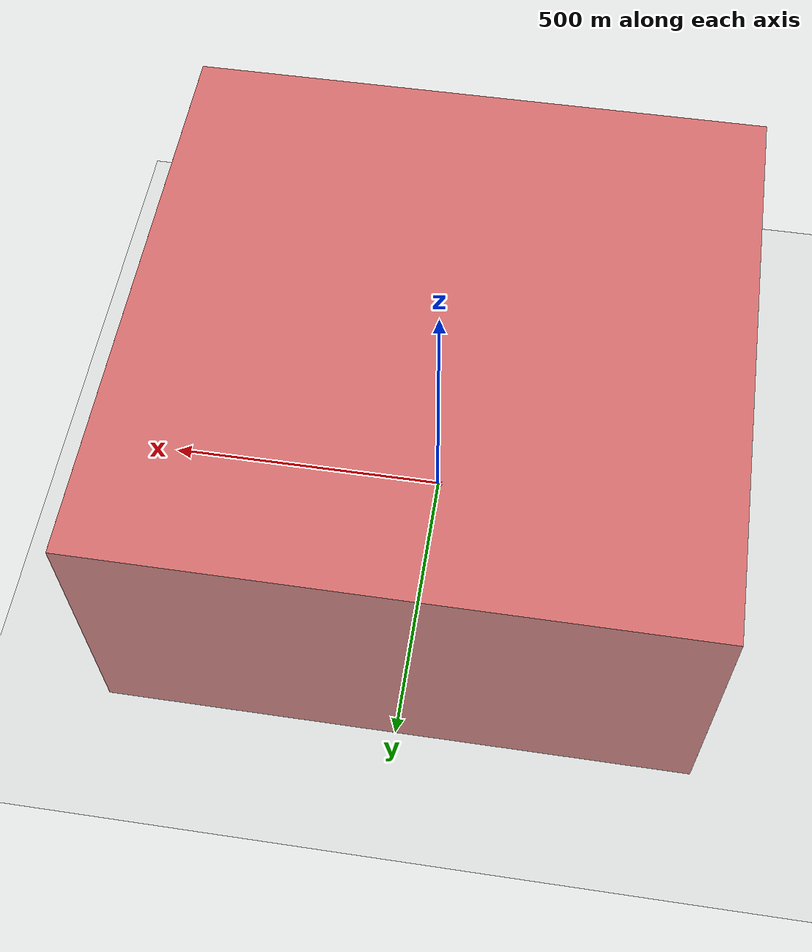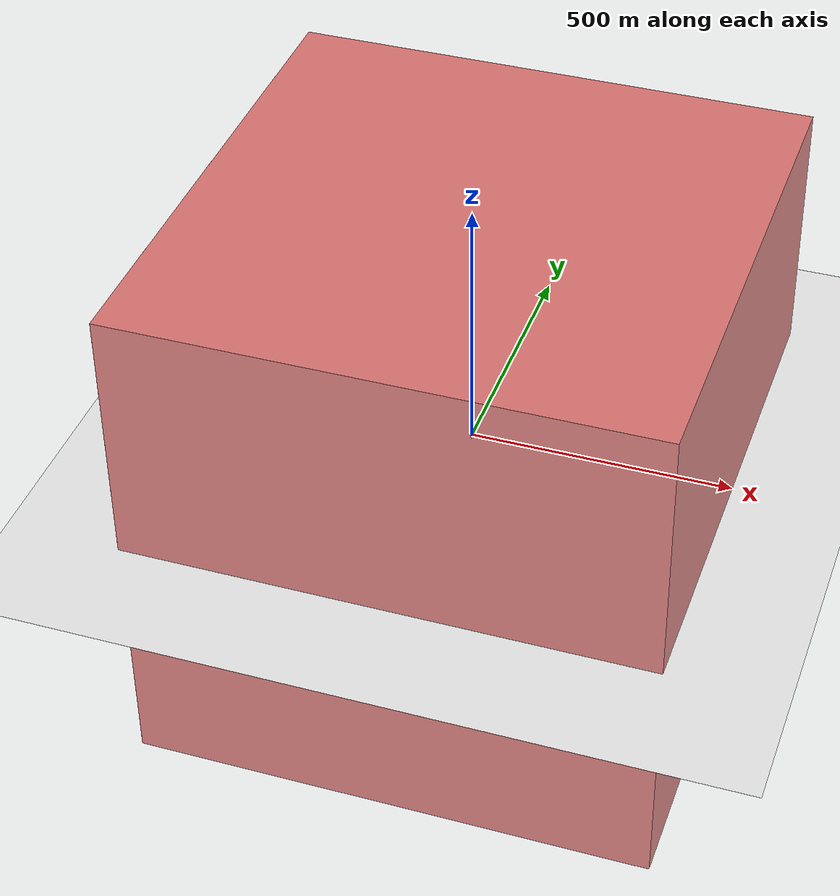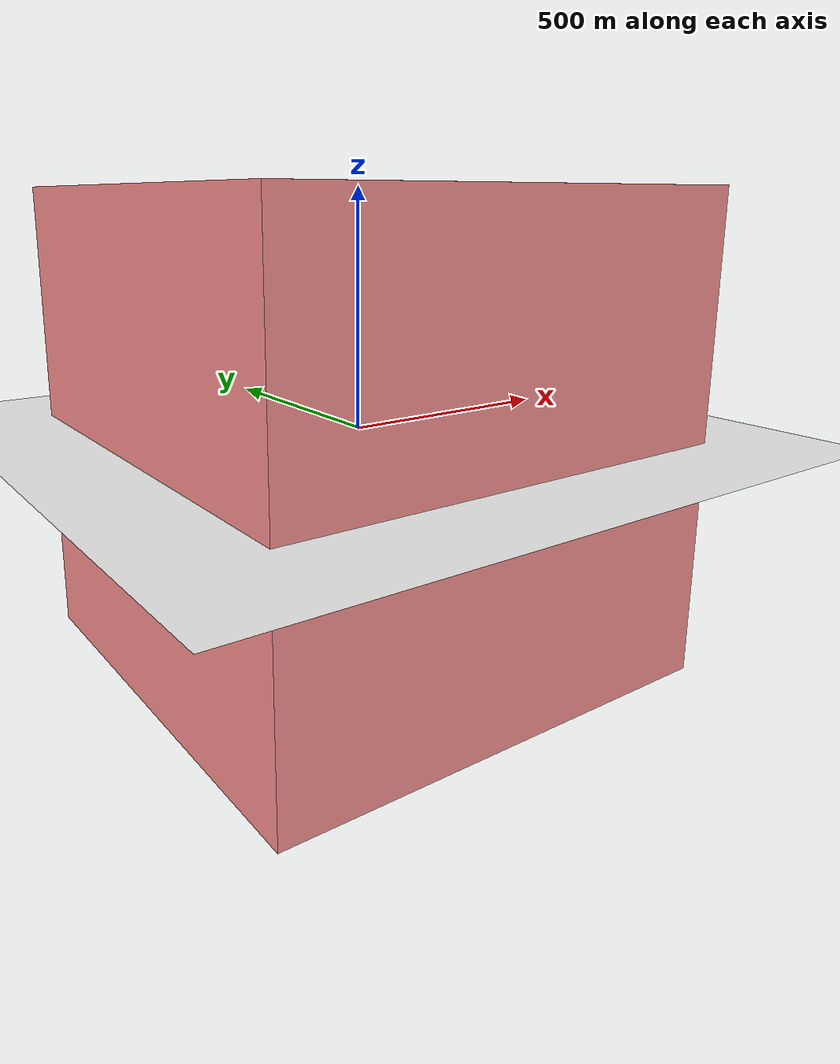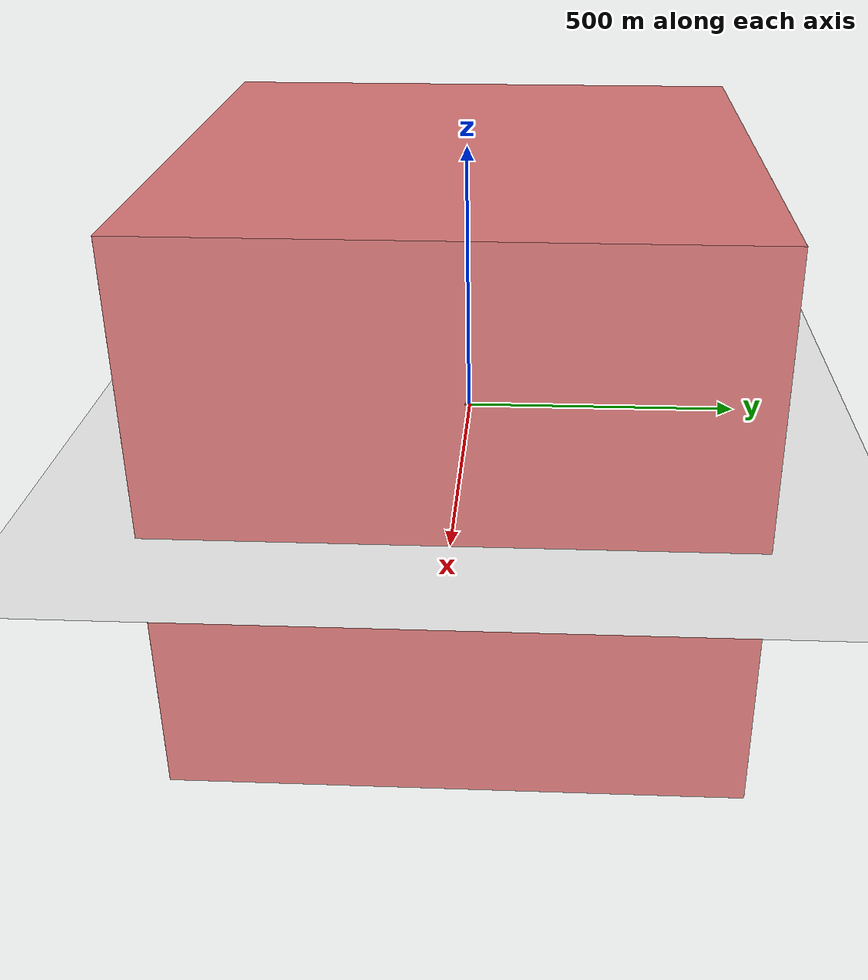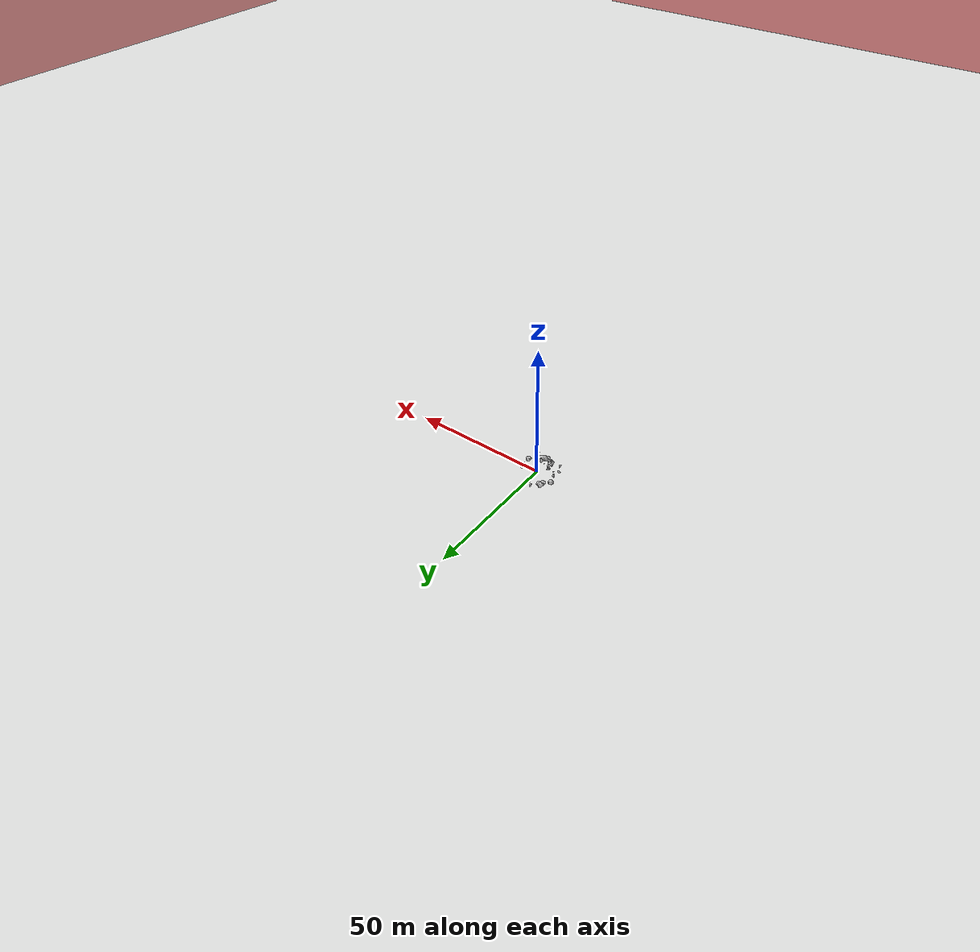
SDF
<sdf version="1.6">
 <world name="default">
  <light name="sun" type="directional">
   <pose>0 0 10 0 -0 0</pose>
   <diffuse>0.8 0.8 0.8 1</diffuse>
   <specular>0.1 0.1 0.1 1</specular>
   <attenuation>
    <range>1000</range>
    <constant>0.9</constant>
    <linear>0.01</linear>
    <quadratic>0.001</quadratic>
   </attenuation>
   <direction>-0.5 0.5 -1</direction>
  </light>
  <gravity>0 0 -9.8</gravity>
  <magnetic_field>6e-06 2.3e-05 -4.2e-05</magnetic_field>
  <atmosphere type="adiabatic"/>
  <physics name="default_physics" default="0" type="ode">
   <max_step_size>0.001</max_step_size>
   <real_time_factor>1</real_time_factor>
   <real_time_update_rate>1000</real_time_update_rate>
  </physics>
  <scene>
   <sky><clouds><speed>12</speed></clouds></sky>
   <ambient>0.4 0.4 0.4 1</ambient>
   <background>0.7 0.7 0.7 1</background>
   <shadows>1</shadows>
  </scene>
  <spherical_coordinates>
   <surface_model>EARTH_WGS84</surface_model>
   <latitude_deg>0</latitude_deg>
   <longitude_deg>0</longitude_deg>
   <elevation>0</elevation>
   <heading_deg>0</heading_deg>
  </spherical_coordinates>
  <model name="rock_bridge">
   <link name="link_2">
    <inertial>
     <mass>1</mass>
     <inertia>
      <ixx>0.166667</ixx>
      <ixy>0</ixy>
      <ixz>0</ixz>
      <iyy>0.166667</iyy>
      <iyz>0</iyz>
      <izz>0.166667</izz>
     </inertia>
    </inertial>
    <visual name="visual">
     <geometry><mesh><uri>model://rock_bridge/rock_bridge.dae</uri><scale>1 1 1</scale></mesh></geometry>
     <material>
      <lighting>1</lighting>
      <script><uri>model://rock_bridge</uri><name>rock_bridge/Diffuse</name></script>
     </material>
    </visual>
    <collision name="collision">
     <geometry><mesh><uri>model://rock_bridge/rock_bridge.dae</uri><scale>1 1 1</scale></mesh></geometry>
     <surface>
      <friction>
       <ode><mu>1</mu><mu2>1</mu2><fdir1>0 0 0</fdir1><slip1>0</slip1><slip2>0</slip2></ode>
       <torsional>
        <coefficient>1</coefficient>
        <patch_radius>0</patch_radius>
        <surface_radius>0</surface_radius>
        <use_patch_radius>1</use_patch_radius>
        <ode><slip>0</slip></ode>
       </torsional>
      </friction>
      <bounce><restitution_coefficient>0</restitution_coefficient><threshold>1e+06</threshold></bounce>
      <contact>
       <collide_without_contact>0</collide_without_contact>
       <collide_without_contact_bitmask>1</collide_without_contact_bitmask>
       <collide_bitmask>1</collide_bitmask>
       <ode>
        <soft_cfm>0</soft_cfm>
        <soft_erp>0.2</soft_erp>
        <kp>1e+13</kp>
        <kd>1</kd>
        <max_vel>0.01</max_vel>
        <min_depth>0</min_depth>
       </ode>
       <bullet>
        <split_impulse>1</split_impulse>
        <split_impulse_penetration_threshold>-0.01</split_impulse_penetration_threshold>
        <soft_cfm>0</soft_cfm>
        <soft_erp>0.2</soft_erp>
        <kp>1e+13</kp>
        <kd>1</kd>
       </bullet>
      </contact>
     </surface>
    </collision>
   </link>
   <static>1</static>
   <pose>-2.3179 -3.71555 0 0 -0 0.214677</pose>
  </model>
  <model name="boulder1">
   <link name="link_0">
    <inertial>
     <mass>1</mass>
     <inertia>
      <ixx>0.166667</ixx>
      <ixy>0</ixy>
      <ixz>0</ixz>
      <iyy>0.166667</iyy>
      <iyz>0</iyz>
      <izz>0.166667</izz>
     </inertia>
    </inertial>
    <visual name="visual">
     <geometry><mesh><uri>model://boulder1/boulder1.dae</uri><scale>1 1 1</scale></mesh></geometry>
     <material>
      <lighting>1</lighting>
      <script><uri>model://boulder1</uri><name>boulder1/Diffuse</name></script>
     </material>
    </visual>
    <collision name="collision">
     <geometry><mesh><uri>model://boulder1/boulder1.dae</uri><scale>1 1 1</scale></mesh></geometry>
     <surface>
      <friction>
       <ode><mu>1</mu><mu2>1</mu2><fdir1>0 0 0</fdir1><slip1>0</slip1><slip2>0</slip2></ode>
       <torsional>
        <coefficient>1</coefficient>
        <patch_radius>0</patch_radius>
        <surface_radius>0</surface_radius>
        <use_patch_radius>1</use_patch_radius>
        <ode><slip>0</slip></ode>
       </torsional>
      </friction>
      <bounce><restitution_coefficient>0</restitution_coefficient><threshold>1e+06</threshold></bounce>
      <contact>
       <collide_without_contact>0</collide_without_contact>
       <collide_without_contact_bitmask>1</collide_without_contact_bitmask>
       <collide_bitmask>1</collide_bitmask>
       <ode>
        <soft_cfm>0</soft_cfm>
        <soft_erp>0.2</soft_erp>
        <kp>1e+13</kp>
        <kd>1</kd>
        <max_vel>0.01</max_vel>
        <min_depth>0</min_depth>
       </ode>
       <bullet>
        <split_impulse>1</split_impulse>
        <split_impulse_penetration_threshold>-0.01</split_impulse_penetration_threshold>
        <soft_cfm>0</soft_cfm>
        <soft_erp>0.2</soft_erp>
        <kp>1e+13</kp>
        <kd>1</kd>
       </bullet>
      </contact>
     </surface>
    </collision>
   </link>
   <static>1</static>
   <pose>-4.50183 4.31712 0 0 0 -1.7041</pose>
  </model>
  <model name="boulder1_0">
   <link name="link_0">
    <inertial>
     <mass>1</mass>
     <inertia>
      <ixx>0.166667</ixx>
      <ixy>0</ixy>
      <ixz>0</ixz>
      <iyy>0.166667</iyy>
      <iyz>0</iyz>
      <izz>0.166667</izz>
     </inertia>
    </inertial>
    <visual name="visual">
     <geometry><mesh><uri>model://boulder1/boulder1.dae</uri><scale>1 1 1</scale></mesh></geometry>
     <material>
      <lighting>1</lighting>
      <script><uri>model://boulder1</uri><name>boulder1/Diffuse</name></script>
     </material>
    </visual>
    <collision name="collision">
     <geometry><mesh><uri>model://boulder1/boulder1.dae</uri><scale>1 1 1</scale></mesh></geometry>
     <surface>
      <friction>
       <ode><mu>1</mu><mu2>1</mu2><fdir1>0 0 0</fdir1><slip1>0</slip1><slip2>0</slip2></ode>
       <torsional>
        <coefficient>1</coefficient>
        <patch_radius>0</patch_radius>
        <surface_radius>0</surface_radius>
        <use_patch_radius>1</use_patch_radius>
        <ode><slip>0</slip></ode>
       </torsional>
      </friction>
      <bounce><restitution_coefficient>0</restitution_coefficient><threshold>1e+06</threshold></bounce>
      <contact>
       <collide_without_contact>0</collide_without_contact>
       <collide_without_contact_bitmask>1</collide_without_contact_bitmask>
       <collide_bitmask>1</collide_bitmask>
       <ode>
        <soft_cfm>0</soft_cfm>
        <soft_erp>0.2</soft_erp>
        <kp>1e+13</kp>
        <kd>1</kd>
        <max_vel>0.01</max_vel>
        <min_depth>0</min_depth>
       </ode>
       <bullet>
        <split_impulse>1</split_impulse>
        <split_impulse_penetration_threshold>-0.01</split_impulse_penetration_threshold>
        <soft_cfm>0</soft_cfm>
        <soft_erp>0.2</soft_erp>
        <kp>1e+13</kp>
        <kd>1</kd>
       </bullet>
      </contact>
     </surface>
    </collision>
   </link>
   <static>1</static>
   <pose>5.56044 -7.40319 0.146204 0.882334 0.311832 2.89433</pose>
  </model>
  <model name="boulder1_1">
   <link name="link_0">
    <inertial>
     <mass>1</mass>
     <inertia>
      <ixx>0.166667</ixx>
      <ixy>0</ixy>
      <ixz>0</ixz>
      <iyy>0.166667</iyy>
      <iyz>0</iyz>
      <izz>0.166667</izz>
     </inertia>
    </inertial>
    <visual name="visual">
     <geometry><mesh><uri>model://boulder1/boulder1.dae</uri><scale>1 1 1</scale></mesh></geometry>
     <material>
      <lighting>1</lighting>
      <script><uri>model://boulder1</uri><name>boulder1/Diffuse</name></script>
     </material>
    </visual>
    <collision name="collision">
     <geometry><mesh><uri>model://boulder1/boulder1.dae</uri><scale>1 1 1</scale></mesh></geometry>
     <surface>
      <friction>
       <ode><mu>1</mu><mu2>1</mu2><fdir1>0 0 0</fdir1><slip1>0</slip1><slip2>0</slip2></ode>
       <torsional>
        <coefficient>1</coefficient>
        <patch_radius>0</patch_radius>
        <surface_radius>0</surface_radius>
        <use_patch_radius>1</use_patch_radius>
        <ode><slip>0</slip></ode>
       </torsional>
      </friction>
      <bounce><restitution_coefficient>0</restitution_coefficient><threshold>1e+06</threshold></bounce>
      <contact>
       <collide_without_contact>0</collide_without_contact>
       <collide_without_contact_bitmask>1</collide_without_contact_bitmask>
       <collide_bitmask>1</collide_bitmask>
       <ode>
        <soft_cfm>0</soft_cfm>
        <soft_erp>0.2</soft_erp>
        <kp>1e+13</kp>
        <kd>1</kd>
        <max_vel>0.01</max_vel>
        <min_depth>0</min_depth>
       </ode>
       <bullet>
        <split_impulse>1</split_impulse>
        <split_impulse_penetration_threshold>-0.01</split_impulse_penetration_threshold>
        <soft_cfm>0</soft_cfm>
        <soft_erp>0.2</soft_erp>
        <kp>1e+13</kp>
        <kd>1</kd>
       </bullet>
      </contact>
     </surface>
    </collision>
   </link>
   <static>1</static>
   <pose>-7.11751 1.92658 0 0 0 -2.76591</pose>
  </model>
  <model name="boulder1_2">
   <link name="link_0">
    <inertial>
     <mass>1</mass>
     <inertia>
      <ixx>0.166667</ixx>
      <ixy>0</ixy>
      <ixz>0</ixz>
      <iyy>0.166667</iyy>
      <iyz>0</iyz>
      <izz>0.166667</izz>
     </inertia>
    </inertial>
    <visual name="visual">
     <geometry><mesh><uri>model://boulder1/boulder1.dae</uri><scale>1 1 1</scale></mesh></geometry>
     <material>
      <lighting>1</lighting>
      <script><uri>model://boulder1</uri><name>boulder1/Diffuse</name></script>
     </material>
    </visual>
    <collision name="collision">
     <geometry><mesh><uri>model://boulder1/boulder1.dae</uri><scale>1 1 1</scale></mesh></geometry>
     <surface>
      <friction>
       <ode><mu>1</mu><mu2>1</mu2><fdir1>0 0 0</fdir1><slip1>0</slip1><slip2>0</slip2></ode>
       <torsional>
        <coefficient>1</coefficient>
        <patch_radius>0</patch_radius>
        <surface_radius>0</surface_radius>
        <use_patch_radius>1</use_patch_radius>
        <ode><slip>0</slip></ode>
       </torsional>
      </friction>
      <bounce><restitution_coefficient>0</restitution_coefficient><threshold>1e+06</threshold></bounce>
      <contact>
       <collide_without_contact>0</collide_without_contact>
       <collide_without_contact_bitmask>1</collide_without_contact_bitmask>
       <collide_bitmask>1</collide_bitmask>
       <ode>
        <soft_cfm>0</soft_cfm>
        <soft_erp>0.2</soft_erp>
        <kp>1e+13</kp>
        <kd>1</kd>
        <max_vel>0.01</max_vel>
        <min_depth>0</min_depth>
       </ode>
       <bullet>
        <split_impulse>1</split_impulse>
        <split_impulse_penetration_threshold>-0.01</split_impulse_penetration_threshold>
        <soft_cfm>0</soft_cfm>
        <soft_erp>0.2</soft_erp>
        <kp>1e+13</kp>
        <kd>1</kd>
       </bullet>
      </contact>
     </surface>
    </collision>
   </link>
   <static>1</static>
   <pose>-5.05483 2.9436 0.147332 0 -0 0</pose>
  </model>
  <model name="boulder2">
   <link name="link_1">
    <inertial>
     <mass>1</mass>
     <inertia>
      <ixx>0.166667</ixx>
      <ixy>0</ixy>
      <ixz>0</ixz>
      <iyy>0.166667</iyy>
      <iyz>0</iyz>
      <izz>0.166667</izz>
     </inertia>
    </inertial>
    <visual name="visual">
     <geometry><mesh><uri>model://boulder2/boulder2.dae</uri><scale>1 1 1</scale></mesh></geometry>
     <material>
      <lighting>1</lighting>
      <script><uri>model://boulder2</uri><name>boulder2/Diffuse</name></script>
     </material>
    </visual>
    <collision name="collision">
     <geometry><mesh><uri>model://boulder2/boulder2.dae</uri><scale>1 1 1</scale></mesh></geometry>
     <surface>
      <friction>
       <ode><mu>1</mu><mu2>1</mu2><fdir1>0 0 0</fdir1><slip1>0</slip1><slip2>0</slip2></ode>
       <torsional>
        <coefficient>1</coefficient>
        <patch_radius>0</patch_radius>
        <surface_radius>0</surface_radius>
        <use_patch_radius>1</use_patch_radius>
        <ode><slip>0</slip></ode>
       </torsional>
      </friction>
      <bounce><restitution_coefficient>0</restitution_coefficient><threshold>1e+06</threshold></bounce>
      <contact>
       <collide_without_contact>0</collide_without_contact>
       <collide_without_contact_bitmask>1</collide_without_contact_bitmask>
       <collide_bitmask>1</collide_bitmask>
       <ode>
        <soft_cfm>0</soft_cfm>
        <soft_erp>0.2</soft_erp>
        <kp>1e+13</kp>
        <kd>1</kd>
        <max_vel>0.01</max_vel>
        <min_depth>0</min_depth>
       </ode>
       <bullet>
        <split_impulse>1</split_impulse>
        <split_impulse_penetration_threshold>-0.01</split_impulse_penetration_threshold>
        <soft_cfm>0</soft_cfm>
        <soft_erp>0.2</soft_erp>
        <kp>1e+13</kp>
        <kd>1</kd>
       </bullet>
      </contact>
     </surface>
    </collision>
   </link>
   <static>1</static>
   <pose>0.7362 5.70189 0 0 -0 1.19676</pose>
  </model>
  <model name="boulder2_0">
   <link name="link_1">
    <inertial>
     <mass>1</mass>
     <inertia>
      <ixx>0.166667</ixx>
      <ixy>0</ixy>
      <ixz>0</ixz>
      <iyy>0.166667</iyy>
      <iyz>0</iyz>
      <izz>0.166667</izz>
     </inertia>
    </inertial>
    <visual name="visual">
     <geometry><mesh><uri>model://boulder2/boulder2.dae</uri><scale>1 1 1</scale></mesh></geometry>
     <material>
      <lighting>1</lighting>
      <script><uri>model://boulder2</uri><name>boulder2/Diffuse</name></script>
     </material>
    </visual>
    <collision name="collision">
     <geometry><mesh><uri>model://boulder2/boulder2.dae</uri><scale>1 1 1</scale></mesh></geometry>
     <surface>
      <friction>
       <ode><mu>1</mu><mu2>1</mu2><fdir1>0 0 0</fdir1><slip1>0</slip1><slip2>0</slip2></ode>
       <torsional>
        <coefficient>1</coefficient>
        <patch_radius>0</patch_radius>
        <surface_radius>0</surface_radius>
        <use_patch_radius>1</use_patch_radius>
        <ode><slip>0</slip></ode>
       </torsional>
      </friction>
      <bounce><restitution_coefficient>0</restitution_coefficient><threshold>1e+06</threshold></bounce>
      <contact>
       <collide_without_contact>0</collide_without_contact>
       <collide_without_contact_bitmask>1</collide_without_contact_bitmask>
       <collide_bitmask>1</collide_bitmask>
       <ode>
        <soft_cfm>0</soft_cfm>
        <soft_erp>0.2</soft_erp>
        <kp>1e+13</kp>
        <kd>1</kd>
        <max_vel>0.01</max_vel>
        <min_depth>0</min_depth>
       </ode>
       <bullet>
        <split_impulse>1</split_impulse>
        <split_impulse_penetration_threshold>-0.01</split_impulse_penetration_threshold>
        <soft_cfm>0</soft_cfm>
        <soft_erp>0.2</soft_erp>
        <kp>1e+13</kp>
        <kd>1</kd>
       </bullet>
      </contact>
     </surface>
    </collision>
   </link>
   <static>1</static>
   <pose>0.141193 6.09005 0 0 -0 2.19582</pose>
  </model>
  <model name="boulder2_1">
   <link name="link_1">
    <inertial>
     <mass>1</mass>
     <inertia>
      <ixx>0.166667</ixx>
      <ixy>0</ixy>
      <ixz>0</ixz>
      <iyy>0.166667</iyy>
      <iyz>0</iyz>
      <izz>0.166667</izz>
     </inertia>
    </inertial>
    <visual name="visual">
     <geometry><mesh><uri>model://boulder2/boulder2.dae</uri><scale>1 1 1</scale></mesh></geometry>
     <material>
      <lighting>1</lighting>
      <script><uri>model://boulder2</uri><name>boulder2/Diffuse</name></script>
     </material>
    </visual>
    <collision name="collision">
     <geometry><mesh><uri>model://boulder2/boulder2.dae</uri><scale>1 1 1</scale></mesh></geometry>
     <surface>
      <friction>
       <ode><mu>1</mu><mu2>1</mu2><fdir1>0 0 0</fdir1><slip1>0</slip1><slip2>0</slip2></ode>
       <torsional>
        <coefficient>1</coefficient>
        <patch_radius>0</patch_radius>
        <surface_radius>0</surface_radius>
        <use_patch_radius>1</use_patch_radius>
        <ode><slip>0</slip></ode>
       </torsional>
      </friction>
      <bounce><restitution_coefficient>0</restitution_coefficient><threshold>1e+06</threshold></bounce>
      <contact>
       <collide_without_contact>0</collide_without_contact>
       <collide_without_contact_bitmask>1</collide_without_contact_bitmask>
       <collide_bitmask>1</collide_bitmask>
       <ode>
        <soft_cfm>0</soft_cfm>
        <soft_erp>0.2</soft_erp>
        <kp>1e+13</kp>
        <kd>1</kd>
        <max_vel>0.01</max_vel>
        <min_depth>0</min_depth>
       </ode>
       <bullet>
        <split_impulse>1</split_impulse>
        <split_impulse_penetration_threshold>-0.01</split_impulse_penetration_threshold>
        <soft_cfm>0</soft_cfm>
        <soft_erp>0.2</soft_erp>
        <kp>1e+13</kp>
        <kd>1</kd>
       </bullet>
      </contact>
     </surface>
    </collision>
   </link>
   <static>1</static>
   <pose>5.61873 0.920096 0.15322 -1.56381 0.000394 -2.18343</pose>
  </model>
  <model name="boulder2_2">
   <link name="link_1">
    <inertial>
     <mass>1</mass>
     <inertia>
      <ixx>0.166667</ixx>
      <ixy>0</ixy>
      <ixz>0</ixz>
      <iyy>0.166667</iyy>
      <iyz>0</iyz>
      <izz>0.166667</izz>
     </inertia>
    </inertial>
    <visual name="visual">
     <geometry><mesh><uri>model://boulder2/boulder2.dae</uri><scale>1 1 1</scale></mesh></geometry>
     <material>
      <lighting>1</lighting>
      <script><uri>model://boulder2</uri><name>boulder2/Diffuse</name></script>
     </material>
    </visual>
    <collision name="collision">
     <geometry><mesh><uri>model://boulder2/boulder2.dae</uri><scale>1 1 1</scale></mesh></geometry>
     <surface>
      <friction>
       <ode><mu>1</mu><mu2>1</mu2><fdir1>0 0 0</fdir1><slip1>0</slip1><slip2>0</slip2></ode>
       <torsional>
        <coefficient>1</coefficient>
        <patch_radius>0</patch_radius>
        <surface_radius>0</surface_radius>
        <use_patch_radius>1</use_patch_radius>
        <ode><slip>0</slip></ode>
       </torsional>
      </friction>
      <bounce><restitution_coefficient>0</restitution_coefficient><threshold>1e+06</threshold></bounce>
      <contact>
       <collide_without_contact>0</collide_without_contact>
       <collide_without_contact_bitmask>1</collide_without_contact_bitmask>
       <collide_bitmask>1</collide_bitmask>
       <ode>
        <soft_cfm>0</soft_cfm>
        <soft_erp>0.2</soft_erp>
        <kp>1e+13</kp>
        <kd>1</kd>
        <max_vel>0.01</max_vel>
        <min_depth>0</min_depth>
       </ode>
       <bullet>
        <split_impulse>1</split_impulse>
        <split_impulse_penetration_threshold>-0.01</split_impulse_penetration_threshold>
        <soft_cfm>0</soft_cfm>
        <soft_erp>0.2</soft_erp>
        <kp>1e+13</kp>
        <kd>1</kd>
       </bullet>
      </contact>
     </surface>
    </collision>
   </link>
   <static>1</static>
   <pose>-6.097 -1.4428 0.064215 -0.066917 -0.736658 -2.06697</pose>
  </model>
  <model name="red_sky_filter">
   <link name="link_1">
    <visual name="visual1">
     <pose>-500 0 0 0 -0 1.5708</pose>
     <geometry><box><size>1000 0.1 1000</size></box></geometry>
     <material>
      <script><name>Gazebo/Red</name><uri>__default__</uri></script>
      <ambient>1 0 0 1</ambient>
      <diffuse>1 0 0 1</diffuse>
      <specular>1 0 0 1</specular>
      <emissive>1 0 0 1</emissive>
     </material>
     <transparency>0.4</transparency>
    </visual>
    <visual name="visual2">
     <pose>500 0 0 0 -0 1.5708</pose>
     <geometry><box><size>1000 0.1 1000</size></box></geometry>
     <material>
      <script><name>Gazebo/Red</name><uri>__default__</uri></script>
      <ambient>1 0 0 1</ambient>
      <diffuse>1 0 0 1</diffuse>
      <specular>1 0 0 1</specular>
      <emissive>1 0 0 1</emissive>
     </material>
     <transparency>0.4</transparency>
    </visual>
    <visual name="visual3">
     <pose>0 500 0 0 -0 0</pose>
     <geometry><box><size>1000 0.1 1000</size></box></geometry>
     <material>
      <script><name>Gazebo/Red</name><uri>__default__</uri></script>
      <ambient>1 0 0 1</ambient>
      <diffuse>1 0 0 1</diffuse>
      <specular>1 0 0 1</specular>
      <emissive>1 0 0 1</emissive>
     </material>
     <transparency>0.4</transparency>
    </visual>
    <visual name="visual4">
     <pose>0 -500 0 0 -0 0</pose>
     <geometry><box><size>1000 0.1 1000</size></box></geometry>
     <material>
      <script><name>Gazebo/Red</name><uri>__default__</uri></script>
      <ambient>1 0 0 1</ambient>
      <diffuse>1 0 0 1</diffuse>
      <specular>1 0 0 1</specular>
      <emissive>1 0 0 1</emissive>
     </material>
     <transparency>0.4</transparency>
    </visual>
    <visual name="visual5">
     <pose>0 0 500 0 -0 0</pose>
     <geometry><box><size>1000 1000 0.1</size></box></geometry>
     <material>
      <script><name>Gazebo/Red</name><uri>__default__</uri></script>
      <ambient>1 0 0 1</ambient>
      <diffuse>1 0 0 1</diffuse>
      <specular>1 0 0 1</specular>
      <emissive>1 0 0 1</emissive>
     </material>
     <transparency>0.4</transparency>
    </visual>
   </link>
   <static>1</static>
  </model>
  <model name="boulder2_2_clone">
   <link name="link_1">
    <inertial>
     <mass>1</mass>
     <inertia>
      <ixx>0.166667</ixx>
      <ixy>0</ixy>
      <ixz>0</ixz>
      <iyy>0.166667</iyy>
      <iyz>0</iyz>
      <izz>0.166667</izz>
     </inertia>
    </inertial>
    <visual name="visual">
     <geometry><mesh><uri>model://boulder2/boulder2.dae</uri><scale>1 1 1</scale></mesh></geometry>
     <material>
      <lighting>1</lighting>
      <script><uri>model://boulder2</uri><name>boulder2/Diffuse</name></script>
     </material>
    </visual>
    <collision name="collision">
     <geometry><mesh><uri>model://boulder2/boulder2.dae</uri><scale>1 1 1</scale></mesh></geometry>
     <surface>
      <friction>
       <ode><mu>1</mu><mu2>1</mu2><fdir1>0 0 0</fdir1><slip1>0</slip1><slip2>0</slip2></ode>
       <torsional>
        <coefficient>1</coefficient>
        <patch_radius>0</patch_radius>
        <surface_radius>0</surface_radius>
        <use_patch_radius>1</use_patch_radius>
        <ode><slip>0</slip></ode>
       </torsional>
      </friction>
      <bounce><restitution_coefficient>0</restitution_coefficient><threshold>1e+06</threshold></bounce>
      <contact>
       <collide_without_contact>0</collide_without_contact>
       <collide_without_contact_bitmask>1</collide_without_contact_bitmask>
       <collide_bitmask>1</collide_bitmask>
       <ode>
        <soft_cfm>0</soft_cfm>
        <soft_erp>0.2</soft_erp>
        <kp>1e+13</kp>
        <kd>1</kd>
        <max_vel>0.01</max_vel>
        <min_depth>0</min_depth>
       </ode>
       <bullet>
        <split_impulse>1</split_impulse>
        <split_impulse_penetration_threshold>-0.01</split_impulse_penetration_threshold>
        <soft_cfm>0</soft_cfm>
        <soft_erp>0.2</soft_erp>
        <kp>1e+13</kp>
        <kd>1</kd>
       </bullet>
      </contact>
     </surface>
    </collision>
   </link>
   <static>1</static>
   <pose>-5.59893 -2.10405 0.064215 -2.35487 0.793674 -2.22416</pose>
  </model>
  <model name="boulder2_2_clone_0">
   <link name="link_1">
    <inertial>
     <mass>1</mass>
     <inertia>
      <ixx>0.166667</ixx>
      <ixy>0</ixy>
      <ixz>0</ixz>
      <iyy>0.166667</iyy>
      <iyz>0</iyz>
      <izz>0.166667</izz>
     </inertia>
    </inertial>
    <visual name="visual">
     <geometry><mesh><uri>model://boulder2/boulder2.dae</uri><scale>1 1 1</scale></mesh></geometry>
     <material>
      <lighting>1</lighting>
      <script><uri>model://boulder2</uri><name>boulder2/Diffuse</name></script>
     </material>
    </visual>
    <collision name="collision">
     <geometry><mesh><uri>model://boulder2/boulder2.dae</uri><scale>1 1 1</scale></mesh></geometry>
     <surface>
      <friction>
       <ode><mu>1</mu><mu2>1</mu2><fdir1>0 0 0</fdir1><slip1>0</slip1><slip2>0</slip2></ode>
       <torsional>
        <coefficient>1</coefficient>
        <patch_radius>0</patch_radius>
        <surface_radius>0</surface_radius>
        <use_patch_radius>1</use_patch_radius>
        <ode><slip>0</slip></ode>
       </torsional>
      </friction>
      <bounce><restitution_coefficient>0</restitution_coefficient><threshold>1e+06</threshold></bounce>
      <contact>
       <collide_without_contact>0</collide_without_contact>
       <collide_without_contact_bitmask>1</collide_without_contact_bitmask>
       <collide_bitmask>1</collide_bitmask>
       <ode>
        <soft_cfm>0</soft_cfm>
        <soft_erp>0.2</soft_erp>
        <kp>1e+13</kp>
        <kd>1</kd>
        <max_vel>0.01</max_vel>
        <min_depth>0</min_depth>
       </ode>
       <bullet>
        <split_impulse>1</split_impulse>
        <split_impulse_penetration_threshold>-0.01</split_impulse_penetration_threshold>
        <soft_cfm>0</soft_cfm>
        <soft_erp>0.2</soft_erp>
        <kp>1e+13</kp>
        <kd>1</kd>
       </bullet>
      </contact>
     </surface>
    </collision>
   </link>
   <static>1</static>
   <pose>-6.08403 -4.372 0.064215 -0.282707 0.680864 1.45135</pose>
  </model>
  <model name="boulder1_1_clone">
   <link name="link_0">
    <inertial>
     <mass>1</mass>
     <inertia>
      <ixx>0.166667</ixx>
      <ixy>0</ixy>
      <ixz>0</ixz>
      <iyy>0.166667</iyy>
      <iyz>0</iyz>
      <izz>0.166667</izz>
     </inertia>
    </inertial>
    <visual name="visual">
     <geometry><mesh><uri>model://boulder1/boulder1.dae</uri><scale>1 1 1</scale></mesh></geometry>
     <material>
      <lighting>1</lighting>
      <script><uri>model://boulder1</uri><name>boulder1/Diffuse</name></script>
     </material>
    </visual>
    <collision name="collision">
     <geometry><mesh><uri>model://boulder1/boulder1.dae</uri><scale>1 1 1</scale></mesh></geometry>
     <surface>
      <friction>
       <ode><mu>1</mu><mu2>1</mu2><fdir1>0 0 0</fdir1><slip1>0</slip1><slip2>0</slip2></ode>
       <torsional>
        <coefficient>1</coefficient>
        <patch_radius>0</patch_radius>
        <surface_radius>0</surface_radius>
        <use_patch_radius>1</use_patch_radius>
        <ode><slip>0</slip></ode>
       </torsional>
      </friction>
      <bounce><restitution_coefficient>0</restitution_coefficient><threshold>1e+06</threshold></bounce>
      <contact>
       <collide_without_contact>0</collide_without_contact>
       <collide_without_contact_bitmask>1</collide_without_contact_bitmask>
       <collide_bitmask>1</collide_bitmask>
       <ode>
        <soft_cfm>0</soft_cfm>
        <soft_erp>0.2</soft_erp>
        <kp>1e+13</kp>
        <kd>1</kd>
        <max_vel>0.01</max_vel>
        <min_depth>0</min_depth>
       </ode>
       <bullet>
        <split_impulse>1</split_impulse>
        <split_impulse_penetration_threshold>-0.01</split_impulse_penetration_threshold>
        <soft_cfm>0</soft_cfm>
        <soft_erp>0.2</soft_erp>
        <kp>1e+13</kp>
        <kd>1</kd>
       </bullet>
      </contact>
     </surface>
    </collision>
   </link>
   <static>1</static>
   <pose>0.977617 -8.08082 0 -1.08313 0 -2.76591</pose>
  </model>
  <model name="boulder1_0_clone">
   <link name="link_0">
    <inertial>
     <mass>1</mass>
     <inertia>
      <ixx>0.166667</ixx>
      <ixy>0</ixy>
      <ixz>0</ixz>
      <iyy>0.166667</iyy>
      <iyz>0</iyz>
      <izz>0.166667</izz>
     </inertia>
    </inertial>
    <visual name="visual">
     <geometry><mesh><uri>model://boulder1/boulder1.dae</uri><scale>1 1 1</scale></mesh></geometry>
     <material>
      <lighting>1</lighting>
      <script><uri>model://boulder1</uri><name>boulder1/Diffuse</name></script>
     </material>
    </visual>
    <collision name="collision">
     <geometry><mesh><uri>model://boulder1/boulder1.dae</uri><scale>1 1 1</scale></mesh></geometry>
     <surface>
      <friction>
       <ode><mu>1</mu><mu2>1</mu2><fdir1>0 0 0</fdir1><slip1>0</slip1><slip2>0</slip2></ode>
       <torsional>
        <coefficient>1</coefficient>
        <patch_radius>0</patch_radius>
        <surface_radius>0</surface_radius>
        <use_patch_radius>1</use_patch_radius>
        <ode><slip>0</slip></ode>
       </torsional>
      </friction>
      <bounce><restitution_coefficient>0</restitution_coefficient><threshold>1e+06</threshold></bounce>
      <contact>
       <collide_without_contact>0</collide_without_contact>
       <collide_without_contact_bitmask>1</collide_without_contact_bitmask>
       <collide_bitmask>1</collide_bitmask>
       <ode>
        <soft_cfm>0</soft_cfm>
        <soft_erp>0.2</soft_erp>
        <kp>1e+13</kp>
        <kd>1</kd>
        <max_vel>0.01</max_vel>
        <min_depth>0</min_depth>
       </ode>
       <bullet>
        <split_impulse>1</split_impulse>
        <split_impulse_penetration_threshold>-0.01</split_impulse_penetration_threshold>
        <soft_cfm>0</soft_cfm>
        <soft_erp>0.2</soft_erp>
        <kp>1e+13</kp>
        <kd>1</kd>
       </bullet>
      </contact>
     </surface>
    </collision>
   </link>
   <static>1</static>
   <pose>5.83806 -4.02079 0.513857 -0.01632 0 0</pose>
  </model>
  <model name="boulder2_2_clone_0_clone">
   <link name="link_1">
    <inertial>
     <mass>1</mass>
     <inertia>
      <ixx>0.166667</ixx>
      <ixy>0</ixy>
      <ixz>0</ixz>
      <iyy>0.166667</iyy>
      <iyz>0</iyz>
      <izz>0.166667</izz>
     </inertia>
    </inertial>
    <visual name="visual">
     <geometry><mesh><uri>model://boulder2/boulder2.dae</uri><scale>1 1 1</scale></mesh></geometry>
     <material>
      <lighting>1</lighting>
      <script><uri>model://boulder2</uri><name>boulder2/Diffuse</name></script>
     </material>
    </visual>
    <collision name="collision">
     <geometry><mesh><uri>model://boulder2/boulder2.dae</uri><scale>1 1 1</scale></mesh></geometry>
     <surface>
      <friction>
       <ode><mu>1</mu><mu2>1</mu2><fdir1>0 0 0</fdir1><slip1>0</slip1><slip2>0</slip2></ode>
       <torsional>
        <coefficient>1</coefficient>
        <patch_radius>0</patch_radius>
        <surface_radius>0</surface_radius>
        <use_patch_radius>1</use_patch_radius>
        <ode><slip>0</slip></ode>
       </torsional>
      </friction>
      <bounce><restitution_coefficient>0</restitution_coefficient><threshold>1e+06</threshold></bounce>
      <contact>
       <collide_without_contact>0</collide_without_contact>
       <collide_without_contact_bitmask>1</collide_without_contact_bitmask>
       <collide_bitmask>1</collide_bitmask>
       <ode>
        <soft_cfm>0</soft_cfm>
        <soft_erp>0.2</soft_erp>
        <kp>1e+13</kp>
        <kd>1</kd>
        <max_vel>0.01</max_vel>
        <min_depth>0</min_depth>
       </ode>
       <bullet>
        <split_impulse>1</split_impulse>
        <split_impulse_penetration_threshold>-0.01</split_impulse_penetration_threshold>
        <soft_cfm>0</soft_cfm>
        <soft_erp>0.2</soft_erp>
        <kp>1e+13</kp>
        <kd>1</kd>
       </bullet>
      </contact>
     </surface>
    </collision>
   </link>
   <static>1</static>
   <pose>-4.82131 -7.49592 0.064215 -0.59155 0.472681 0</pose>
  </model>
  <model name="boulder2_2_clone_clone">
   <link name="link_1">
    <inertial>
     <mass>1</mass>
     <inertia>
      <ixx>0.166667</ixx>
      <ixy>0</ixy>
      <ixz>0</ixz>
      <iyy>0.166667</iyy>
      <iyz>0</iyz>
      <izz>0.166667</izz>
     </inertia>
    </inertial>
    <visual name="visual">
     <geometry><mesh><uri>model://boulder2/boulder2.dae</uri><scale>1 1 1</scale></mesh></geometry>
     <material>
      <lighting>1</lighting>
      <script><uri>model://boulder2</uri><name>boulder2/Diffuse</name></script>
     </material>
    </visual>
    <collision name="collision">
     <geometry><mesh><uri>model://boulder2/boulder2.dae</uri><scale>1 1 1</scale></mesh></geometry>
     <surface>
      <friction>
       <ode><mu>1</mu><mu2>1</mu2><fdir1>0 0 0</fdir1><slip1>0</slip1><slip2>0</slip2></ode>
       <torsional>
        <coefficient>1</coefficient>
        <patch_radius>0</patch_radius>
        <surface_radius>0</surface_radius>
        <use_patch_radius>1</use_patch_radius>
        <ode><slip>0</slip></ode>
       </torsional>
      </friction>
      <bounce><restitution_coefficient>0</restitution_coefficient><threshold>1e+06</threshold></bounce>
      <contact>
       <collide_without_contact>0</collide_without_contact>
       <collide_without_contact_bitmask>1</collide_without_contact_bitmask>
       <collide_bitmask>1</collide_bitmask>
       <ode>
        <soft_cfm>0</soft_cfm>
        <soft_erp>0.2</soft_erp>
        <kp>1e+13</kp>
        <kd>1</kd>
        <max_vel>0.01</max_vel>
        <min_depth>0</min_depth>
       </ode>
       <bullet>
        <split_impulse>1</split_impulse>
        <split_impulse_penetration_threshold>-0.01</split_impulse_penetration_threshold>
        <soft_cfm>0</soft_cfm>
        <soft_erp>0.2</soft_erp>
        <kp>1e+13</kp>
        <kd>1</kd>
       </bullet>
      </contact>
     </surface>
    </collision>
   </link>
   <static>1</static>
   <pose>6.39137 -1.12134 0.064215 -0.59155 0.472681 0</pose>
  </model>
  <model name="boulder2_2_clone_clone_0">
   <link name="link_1">
    <inertial>
     <mass>1</mass>
     <inertia>
      <ixx>0.166667</ixx>
      <ixy>0</ixy>
      <ixz>0</ixz>
      <iyy>0.166667</iyy>
      <iyz>0</iyz>
      <izz>0.166667</izz>
     </inertia>
    </inertial>
    <visual name="visual">
     <geometry><mesh><uri>model://boulder2/boulder2.dae</uri><scale>1 1 1</scale></mesh></geometry>
     <material>
      <lighting>1</lighting>
      <script><uri>model://boulder2</uri><name>boulder2/Diffuse</name></script>
     </material>
    </visual>
    <collision name="collision">
     <geometry><mesh><uri>model://boulder2/boulder2.dae</uri><scale>1 1 1</scale></mesh></geometry>
     <surface>
      <friction>
       <ode><mu>1</mu><mu2>1</mu2><fdir1>0 0 0</fdir1><slip1>0</slip1><slip2>0</slip2></ode>
       <torsional>
        <coefficient>1</coefficient>
        <patch_radius>0</patch_radius>
        <surface_radius>0</surface_radius>
        <use_patch_radius>1</use_patch_radius>
        <ode><slip>0</slip></ode>
       </torsional>
      </friction>
      <bounce><restitution_coefficient>0</restitution_coefficient><threshold>1e+06</threshold></bounce>
      <contact>
       <collide_without_contact>0</collide_without_contact>
       <collide_without_contact_bitmask>1</collide_without_contact_bitmask>
       <collide_bitmask>1</collide_bitmask>
       <ode>
        <soft_cfm>0</soft_cfm>
        <soft_erp>0.2</soft_erp>
        <kp>1e+13</kp>
        <kd>1</kd>
        <max_vel>0.01</max_vel>
        <min_depth>0</min_depth>
       </ode>
       <bullet>
        <split_impulse>1</split_impulse>
        <split_impulse_penetration_threshold>-0.01</split_impulse_penetration_threshold>
        <soft_cfm>0</soft_cfm>
        <soft_erp>0.2</soft_erp>
        <kp>1e+13</kp>
        <kd>1</kd>
       </bullet>
      </contact>
     </surface>
    </collision>
   </link>
   <static>1</static>
   <pose>-2.01647 6.38627 0.064215 -0.59155 0.472681 0</pose>
  </model>
  <model name="boulder1_1_clone_0">
   <link name="link_0">
    <inertial>
     <mass>1</mass>
     <inertia>
      <ixx>0.166667</ixx>
      <ixy>0</ixy>
      <ixz>0</ixz>
      <iyy>0.166667</iyy>
      <iyz>0</iyz>
      <izz>0.166667</izz>
     </inertia>
    </inertial>
    <visual name="visual">
     <geometry><mesh><uri>model://boulder1/boulder1.dae</uri><scale>1 1 1</scale></mesh></geometry>
     <material>
      <lighting>1</lighting>
      <script><uri>model://boulder1</uri><name>boulder1/Diffuse</name></script>
     </material>
    </visual>
    <collision name="collision">
     <geometry><mesh><uri>model://boulder1/boulder1.dae</uri><scale>1 1 1</scale></mesh></geometry>
     <surface>
      <friction>
       <ode><mu>1</mu><mu2>1</mu2><fdir1>0 0 0</fdir1><slip1>0</slip1><slip2>0</slip2></ode>
       <torsional>
        <coefficient>1</coefficient>
        <patch_radius>0</patch_radius>
        <surface_radius>0</surface_radius>
        <use_patch_radius>1</use_patch_radius>
        <ode><slip>0</slip></ode>
       </torsional>
      </friction>
      <bounce><restitution_coefficient>0</restitution_coefficient><threshold>1e+06</threshold></bounce>
      <contact>
       <collide_without_contact>0</collide_without_contact>
       <collide_without_contact_bitmask>1</collide_without_contact_bitmask>
       <collide_bitmask>1</collide_bitmask>
       <ode>
        <soft_cfm>0</soft_cfm>
        <soft_erp>0.2</soft_erp>
        <kp>1e+13</kp>
        <kd>1</kd>
        <max_vel>0.01</max_vel>
        <min_depth>0</min_depth>
       </ode>
       <bullet>
        <split_impulse>1</split_impulse>
        <split_impulse_penetration_threshold>-0.01</split_impulse_penetration_threshold>
        <soft_cfm>0</soft_cfm>
        <soft_erp>0.2</soft_erp>
        <kp>1e+13</kp>
        <kd>1</kd>
       </bullet>
      </contact>
     </surface>
    </collision>
   </link>
   <static>1</static>
   <pose>-5.24973 5.09632 0 1.11464 -0 -2.10771</pose>
  </model>
  <model name="ground_plane">
   <static>1</static>
   <link name="link">
    <collision name="collision">
     <geometry><plane><normal>0 0 1</normal><size>100 100</size></plane></geometry>
     <surface><friction><ode><mu>100</mu><mu2>50</mu2></ode></friction></surface>
    </collision>
    <visual name="visual">
     <cast_shadows>0</cast_shadows>
     <geometry><plane><normal>0 0 1</normal><size>100 100</size></plane></geometry>
     <material>
      <script><uri>file://media/materials/scripts/gazebo.material</uri><name>Gazebo/Grey</name></script>
     </material>
    </visual>
   </link>
  </model>
  <model name="at0">
   <static>0</static>
   <link name="link">
    <inertial>
     <mass>0.01</mass>
     <inertia><ixx>4e-05</ixx><ixy>0</ixy><ixz>0</ixz><iyy>4e-05</iyy><iyz>0</iyz><izz>4e-05</izz></inertia>
    </inertial>
    <visual name="visual">
     <geometry><box><size>0.05 0.05 0.05</size></box></geometry>
     <material>
      <script>
       <uri>model://at0/materials/scripts</uri>
       <uri>model://at0/materials/textures</uri>
       <name>at0/Diffuse</name>
      </script>
     </material>
    </visual>
    <collision name="collision">
     <geometry><box><size>0.05 0.05 0.05</size></box></geometry>
     <surface><friction><ode><mu>0.8</mu><mu2>0.7</mu2></ode></friction></surface>
    </collision>
   </link>
   <pose>-6.40949 -0.430538 0.045 0 -0 0</pose>
  </model>
  <model name="at0_0">
   <static>0</static>
   <link name="link">
    <inertial>
     <mass>0.01</mass>
     <inertia><ixx>4e-05</ixx><ixy>0</ixy><ixz>0</ixz><iyy>4e-05</iyy><iyz>0</iyz><izz>4e-05</izz></inertia>
    </inertial>
    <visual name="visual">
     <geometry><box><size>0.05 0.05 0.05</size></box></geometry>
     <material>
      <script>
       <uri>model://at0/materials/scripts</uri>
       <uri>model://at0/materials/textures</uri>
       <name>at0/Diffuse</name>
      </script>
     </material>
    </visual>
    <collision name="collision">
     <geometry><box><size>0.05 0.05 0.05</size></box></geometry>
     <surface><friction><ode><mu>0.8</mu><mu2>0.7</mu2></ode></friction></surface>
    </collision>
   </link>
   <pose>-6.40589 -0.523574 0.045 0 -0 0</pose>
  </model>
  <model name="at0_1">
   <static>0</static>
   <link name="link">
    <inertial>
     <mass>0.01</mass>
     <inertia><ixx>4e-05</ixx><ixy>0</ixy><ixz>0</ixz><iyy>4e-05</iyy><iyz>0</iyz><izz>4e-05</izz></inertia>
    </inertial>
    <visual name="visual">
     <geometry><box><size>0.05 0.05 0.05</size></box></geometry>
     <material>
      <script>
       <uri>model://at0/materials/scripts</uri>
       <uri>model://at0/materials/textures</uri>
       <name>at0/Diffuse</name>
      </script>
     </material>
    </visual>
    <collision name="collision">
     <geometry><box><size>0.05 0.05 0.05</size></box></geometry>
     <surface><friction><ode><mu>0.8</mu><mu2>0.7</mu2></ode></friction></surface>
    </collision>
   </link>
   <pose>-6.49581 -0.5221 0.045 0 -0 0</pose>
  </model>
  <model name="at0_2">
   <static>0</static>
   <link name="link">
    <inertial>
     <mass>0.01</mass>
     <inertia><ixx>4e-05</ixx><ixy>0</ixy><ixz>0</ixz><iyy>4e-05</iyy><iyz>0</iyz><izz>4e-05</izz></inertia>
    </inertial>
    <visual name="visual">
     <geometry><box><size>0.05 0.05 0.05</size></box></geometry>
     <material>
      <script>
       <uri>model://at0/materials/scripts</uri>
       <uri>model://at0/materials/textures</uri>
       <name>at0/Diffuse</name>
      </script>
     </material>
    </visual>
    <collision name="collision">
     <geometry><box><size>0.05 0.05 0.05</size></box></geometry>
     <surface><friction><ode><mu>0.8</mu><mu2>0.7</mu2></ode></friction></surface>
    </collision>
   </link>
   <pose>-6.31735 -0.522905 0.045 0 -0 0</pose>
  </model>
  <model name="at0_3">
   <static>0</static>
   <link name="link">
    <inertial>
     <mass>0.01</mass>
     <inertia><ixx>4e-05</ixx><ixy>0</ixy><ixz>0</ixz><iyy>4e-05</iyy><iyz>0</iyz><izz>4e-05</izz></inertia>
    </inertial>
    <visual name="visual">
     <geometry><box><size>0.05 0.05 0.05</size></box></geometry>
     <material>
      <script>
       <uri>model://at0/materials/scripts</uri>
       <uri>model://at0/materials/textures</uri>
       <name>at0/Diffuse</name>
      </script>
     </material>
    </visual>
    <collision name="collision">
     <geometry><box><size>0.05 0.05 0.05</size></box></geometry>
     <surface><friction><ode><mu>0.8</mu><mu2>0.7</mu2></ode></friction></surface>
    </collision>
   </link>
   <pose>-6.49905 -0.428971 0.045 0 -0 0</pose>
  </model>
  <model name="at0_4">
   <static>0</static>
   <link name="link">
    <inertial>
     <mass>0.01</mass>
     <inertia><ixx>4e-05</ixx><ixy>0</ixy><ixz>0</ixz><iyy>4e-05</iyy><iyz>0</iyz><izz>4e-05</izz></inertia>
    </inertial>
    <visual name="visual">
     <geometry><box><size>0.05 0.05 0.05</size></box></geometry>
     <material>
      <script>
       <uri>model://at0/materials/scripts</uri>
       <uri>model://at0/materials/textures</uri>
       <name>at0/Diffuse</name>
      </script>
     </material>
    </visual>
    <collision name="collision">
     <geometry><box><size>0.05 0.05 0.05</size></box></geometry>
     <surface><friction><ode><mu>0.8</mu><mu2>0.7</mu2></ode></friction></surface>
    </collision>
   </link>
   <pose>-6.31512 -0.424897 0.045 0 -0 0</pose>
  </model>
  <model name="at0_5">
   <static>0</static>
   <link name="link">
    <inertial>
     <mass>0.01</mass>
     <inertia><ixx>4e-05</ixx><ixy>0</ixy><ixz>0</ixz><iyy>4e-05</iyy><iyz>0</iyz><izz>4e-05</izz></inertia>
    </inertial>
    <visual name="visual">
     <geometry><box><size>0.05 0.05 0.05</size></box></geometry>
     <material>
      <script>
       <uri>model://at0/materials/scripts</uri>
       <uri>model://at0/materials/textures</uri>
       <name>at0/Diffuse</name>
      </script>
     </material>
    </visual>
    <collision name="collision">
     <geometry><box><size>0.05 0.05 0.05</size></box></geometry>
     <surface><friction><ode><mu>0.8</mu><mu2>0.7</mu2></ode></friction></surface>
    </collision>
   </link>
   <pose>-6.50173 -0.322517 0.045 0 -0 0</pose>
  </model>
  <model name="at0_6">
   <static>0</static>
   <link name="link">
    <inertial>
     <mass>0.01</mass>
     <inertia><ixx>4e-05</ixx><ixy>0</ixy><ixz>0</ixz><iyy>4e-05</iyy><iyz>0</iyz><izz>4e-05</izz></inertia>
    </inertial>
    <visual name="visual">
     <geometry><box><size>0.05 0.05 0.05</size></box></geometry>
     <material>
      <script>
       <uri>model://at0/materials/scripts</uri>
       <uri>model://at0/materials/textures</uri>
       <name>at0/Diffuse</name>
      </script>
     </material>
    </visual>
    <collision name="collision">
     <geometry><box><size>0.05 0.05 0.05</size></box></geometry>
     <surface><friction><ode><mu>0.8</mu><mu2>0.7</mu2></ode></friction></surface>
    </collision>
   </link>
   <pose>-6.41147 -0.316812 0.045 0 -0 0</pose>
  </model>
  <model name="at0_7">
   <static>0</static>
   <link name="link">
    <inertial>
     <mass>0.01</mass>
     <inertia><ixx>4e-05</ixx><ixy>0</ixy><ixz>0</ixz><iyy>4e-05</iyy><iyz>0</iyz><izz>4e-05</izz></inertia>
    </inertial>
    <visual name="visual">
     <geometry><box><size>0.05 0.05 0.05</size></box></geometry>
     <material>
      <script>
       <uri>model://at0/materials/scripts</uri>
       <uri>model://at0/materials/textures</uri>
       <name>at0/Diffuse</name>
      </script>
     </material>
    </visual>
    <collision name="collision">
     <geometry><box><size>0.05 0.05 0.05</size></box></geometry>
     <surface><friction><ode><mu>0.8</mu><mu2>0.7</mu2></ode></friction></surface>
    </collision>
   </link>
   <pose>-6.31812 -0.321464 0.045 0 -0 0</pose>
  </model>
  <model name="at0_8">
   <static>0</static>
   <link name="link">
    <inertial>
     <mass>0.01</mass>
     <inertia><ixx>4e-05</ixx><ixy>0</ixy><ixz>0</ixz><iyy>4e-05</iyy><iyz>0</iyz><izz>4e-05</izz></inertia>
    </inertial>
    <visual name="visual">
     <geometry><box><size>0.05 0.05 0.05</size></box></geometry>
     <material>
      <script>
       <uri>model://at0/materials/scripts</uri>
       <uri>model://at0/materials/textures</uri>
       <name>at0/Diffuse</name>
      </script>
     </material>
    </visual>
    <collision name="collision">
     <geometry><box><size>0.05 0.05 0.05</size></box></geometry>
     <surface><friction><ode><mu>0.8</mu><mu2>0.7</mu2></ode></friction></surface>
    </collision>
   </link>
   <pose>4.36817 -4.50026 0.045 0 -0 0</pose>
  </model>
  <model name="at0_9">
   <static>0</static>
   <link name="link">
    <inertial>
     <mass>0.01</mass>
     <inertia><ixx>4e-05</ixx><ixy>0</ixy><ixz>0</ixz><iyy>4e-05</iyy><iyz>0</iyz><izz>4e-05</izz></inertia>
    </inertial>
    <visual name="visual">
     <geometry><box><size>0.05 0.05 0.05</size></box></geometry>
     <material>
      <script>
       <uri>model://at0/materials/scripts</uri>
       <uri>model://at0/materials/textures</uri>
       <name>at0/Diffuse</name>
      </script>
     </material>
    </visual>
    <collision name="collision">
     <geometry><box><size>0.05 0.05 0.05</size></box></geometry>
     <surface><friction><ode><mu>0.8</mu><mu2>0.7</mu2></ode></friction></surface>
    </collision>
   </link>
   <pose>4.44043 -4.56995 0.045 0 -0 0</pose>
  </model>
  <model name="at0_10">
   <static>0</static>
   <link name="link">
    <inertial>
     <mass>0.01</mass>
     <inertia><ixx>4e-05</ixx><ixy>0</ixy><ixz>0</ixz><iyy>4e-05</iyy><iyz>0</iyz><izz>4e-05</izz></inertia>
    </inertial>
    <visual name="visual">
     <geometry><box><size>0.05 0.05 0.05</size></box></geometry>
     <material>
      <script>
       <uri>model://at0/materials/scripts</uri>
       <uri>model://at0/materials/textures</uri>
       <name>at0/Diffuse</name>
      </script>
     </material>
    </visual>
    <collision name="collision">
     <geometry><box><size>0.05 0.05 0.05</size></box></geometry>
     <surface><friction><ode><mu>0.8</mu><mu2>0.7</mu2></ode></friction></surface>
    </collision>
   </link>
   <pose>4.52263 -4.64063 0.045 0 -0 0</pose>
  </model>
  <model name="at0_11">
   <static>0</static>
   <link name="link">
    <inertial>
     <mass>0.01</mass>
     <inertia><ixx>4e-05</ixx><ixy>0</ixy><ixz>0</ixz><iyy>4e-05</iyy><iyz>0</iyz><izz>4e-05</izz></inertia>
    </inertial>
    <visual name="visual">
     <geometry><box><size>0.05 0.05 0.05</size></box></geometry>
     <material>
      <script>
       <uri>model://at0/materials/scripts</uri>
       <uri>model://at0/materials/textures</uri>
       <name>at0/Diffuse</name>
      </script>
     </material>
    </visual>
    <collision name="collision">
     <geometry><box><size>0.05 0.05 0.05</size></box></geometry>
     <surface><friction><ode><mu>0.8</mu><mu2>0.7</mu2></ode></friction></surface>
    </collision>
   </link>
   <pose>4.60031 -4.71447 0.045 0 -0 0</pose>
  </model>
  <model name="at0_12">
   <static>0</static>
   <link name="link">
    <inertial>
     <mass>0.01</mass>
     <inertia><ixx>4e-05</ixx><ixy>0</ixy><ixz>0</ixz><iyy>4e-05</iyy><iyz>0</iyz><izz>4e-05</izz></inertia>
    </inertial>
    <visual name="visual">
     <geometry><box><size>0.05 0.05 0.05</size></box></geometry>
     <material>
      <script>
       <uri>model://at0/materials/scripts</uri>
       <uri>model://at0/materials/textures</uri>
       <name>at0/Diffuse</name>
      </script>
     </material>
    </visual>
    <collision name="collision">
     <geometry><box><size>0.05 0.05 0.05</size></box></geometry>
     <surface><friction><ode><mu>0.8</mu><mu2>0.7</mu2></ode></friction></surface>
    </collision>
   </link>
   <pose>5.00629 2.0256 0.045 0 -0 0</pose>
  </model>
  <model name="at0_13">
   <static>0</static>
   <link name="link">
    <inertial>
     <mass>0.01</mass>
     <inertia><ixx>4e-05</ixx><ixy>0</ixy><ixz>0</ixz><iyy>4e-05</iyy><iyz>0</iyz><izz>4e-05</izz></inertia>
    </inertial>
    <visual name="visual">
     <geometry><box><size>0.05 0.05 0.05</size></box></geometry>
     <material>
      <script>
       <uri>model://at0/materials/scripts</uri>
       <uri>model://at0/materials/textures</uri>
       <name>at0/Diffuse</name>
      </script>
     </material>
    </visual>
    <collision name="collision">
     <geometry><box><size>0.05 0.05 0.05</size></box></geometry>
     <surface><friction><ode><mu>0.8</mu><mu2>0.7</mu2></ode></friction></surface>
    </collision>
   </link>
   <pose>4.91775 2.0321 0.045 0 -0 0</pose>
  </model>
  <model name="at0_14">
   <static>0</static>
   <link name="link">
    <inertial>
     <mass>0.01</mass>
     <inertia><ixx>4e-05</ixx><ixy>0</ixy><ixz>0</ixz><iyy>4e-05</iyy><iyz>0</iyz><izz>4e-05</izz></inertia>
    </inertial>
    <visual name="visual">
     <geometry><box><size>0.05 0.05 0.05</size></box></geometry>
     <material>
      <script>
       <uri>model://at0/materials/scripts</uri>
       <uri>model://at0/materials/textures</uri>
       <name>at0/Diffuse</name>
      </script>
     </material>
    </visual>
    <collision name="collision">
     <geometry><box><size>0.05 0.05 0.05</size></box></geometry>
     <surface><friction><ode><mu>0.8</mu><mu2>0.7</mu2></ode></friction></surface>
    </collision>
   </link>
   <pose>5.11198 2.03767 0.045 0 -0 0</pose>
  </model>
  <model name="at0_15">
   <static>0</static>
   <link name="link">
    <inertial>
     <mass>0.01</mass>
     <inertia><ixx>4e-05</ixx><ixy>0</ixy><ixz>0</ixz><iyy>4e-05</iyy><iyz>0</iyz><izz>4e-05</izz></inertia>
    </inertial>
    <visual name="visual">
     <geometry><box><size>0.05 0.05 0.05</size></box></geometry>
     <material>
      <script>
       <uri>model://at0/materials/scripts</uri>
       <uri>model://at0/materials/textures</uri>
       <name>at0/Diffuse</name>
      </script>
     </material>
    </visual>
    <collision name="collision">
     <geometry><box><size>0.05 0.05 0.05</size></box></geometry>
     <surface><friction><ode><mu>0.8</mu><mu2>0.7</mu2></ode></friction></surface>
    </collision>
   </link>
   <pose>4.80952 2.03987 0.045 0 -0 0</pose>
  </model>
  <model name="at0_16">
   <static>0</static>
   <link name="link">
    <inertial>
     <mass>0.01</mass>
     <inertia><ixx>4e-05</ixx><ixy>0</ixy><ixz>0</ixz><iyy>4e-05</iyy><iyz>0</iyz><izz>4e-05</izz></inertia>
    </inertial>
    <visual name="visual">
     <geometry><box><size>0.05 0.05 0.05</size></box></geometry>
     <material>
      <script>
       <uri>model://at0/materials/scripts</uri>
       <uri>model://at0/materials/textures</uri>
       <name>at0/Diffuse</name>
      </script>
     </material>
    </visual>
    <collision name="collision">
     <geometry><box><size>0.05 0.05 0.05</size></box></geometry>
     <surface><friction><ode><mu>0.8</mu><mu2>0.7</mu2></ode></friction></surface>
    </collision>
   </link>
   <pose>5.20401 2.03143 0.045 0 -0 0</pose>
  </model>
  <model name="at0_17">
   <static>0</static>
   <link name="link">
    <inertial>
     <mass>0.01</mass>
     <inertia><ixx>4e-05</ixx><ixy>0</ixy><ixz>0</ixz><iyy>4e-05</iyy><iyz>0</iyz><izz>4e-05</izz></inertia>
    </inertial>
    <visual name="visual">
     <geometry><box><size>0.05 0.05 0.05</size></box></geometry>
     <material>
      <script>
       <uri>model://at0/materials/scripts</uri>
       <uri>model://at0/materials/textures</uri>
       <name>at0/Diffuse</name>
      </script>
     </material>
    </visual>
    <collision name="collision">
     <geometry><box><size>0.05 0.05 0.05</size></box></geometry>
     <surface><friction><ode><mu>0.8</mu><mu2>0.7</mu2></ode></friction></surface>
    </collision>
   </link>
   <pose>5.00356 1.91692 0.045 0 -0 0</pose>
  </model>
  <model name="at0_18">
   <static>0</static>
   <link name="link">
    <inertial>
     <mass>0.01</mass>
     <inertia><ixx>4e-05</ixx><ixy>0</ixy><ixz>0</ixz><iyy>4e-05</iyy><iyz>0</iyz><izz>4e-05</izz></inertia>
    </inertial>
    <visual name="visual">
     <geometry><box><size>0.05 0.05 0.05</size></box></geometry>
     <material>
      <script>
       <uri>model://at0/materials/scripts</uri>
       <uri>model://at0/materials/textures</uri>
       <name>at0/Diffuse</name>
      </script>
     </material>
    </visual>
    <collision name="collision">
     <geometry><box><size>0.05 0.05 0.05</size></box></geometry>
     <surface><friction><ode><mu>0.8</mu><mu2>0.7</mu2></ode></friction></surface>
    </collision>
   </link>
   <pose>5.01128 2.14067 0.045 0 -0 0</pose>
  </model>
  <model name="at0_19">
   <static>0</static>
   <link name="link">
    <inertial>
     <mass>0.01</mass>
     <inertia><ixx>4e-05</ixx><ixy>0</ixy><ixz>0</ixz><iyy>4e-05</iyy><iyz>0</iyz><izz>4e-05</izz></inertia>
    </inertial>
    <visual name="visual">
     <geometry><box><size>0.05 0.05 0.05</size></box></geometry>
     <material>
      <script>
       <uri>model://at0/materials/scripts</uri>
       <uri>model://at0/materials/textures</uri>
       <name>at0/Diffuse</name>
      </script>
     </material>
    </visual>
    <collision name="collision">
     <geometry><box><size>0.05 0.05 0.05</size></box></geometry>
     <surface><friction><ode><mu>0.8</mu><mu2>0.7</mu2></ode></friction></surface>
    </collision>
   </link>
   <pose>5.01094 1.8122 0.045 0 -0 0</pose>
  </model>
  <model name="at0_20">
   <static>0</static>
   <link name="link">
    <inertial>
     <mass>0.01</mass>
     <inertia><ixx>4e-05</ixx><ixy>0</ixy><ixz>0</ixz><iyy>4e-05</iyy><iyz>0</iyz><izz>4e-05</izz></inertia>
    </inertial>
    <visual name="visual">
     <geometry><box><size>0.05 0.05 0.05</size></box></geometry>
     <material>
      <script>
       <uri>model://at0/materials/scripts</uri>
       <uri>model://at0/materials/textures</uri>
       <name>at0/Diffuse</name>
      </script>
     </material>
    </visual>
    <collision name="collision">
     <geometry><box><size>0.05 0.05 0.05</size></box></geometry>
     <surface><friction><ode><mu>0.8</mu><mu2>0.7</mu2></ode></friction></surface>
    </collision>
   </link>
   <pose>5.01438 2.26492 0.045 0 -0 0</pose>
  </model>
  <model name="at0_21">
   <static>0</static>
   <link name="link">
    <inertial>
     <mass>0.01</mass>
     <inertia><ixx>4e-05</ixx><ixy>0</ixy><ixz>0</ixz><iyy>4e-05</iyy><iyz>0</iyz><izz>4e-05</izz></inertia>
    </inertial>
    <visual name="visual">
     <geometry><box><size>0.05 0.05 0.05</size></box></geometry>
     <material>
      <script>
       <uri>model://at0/materials/scripts</uri>
       <uri>model://at0/materials/textures</uri>
       <name>at0/Diffuse</name>
      </script>
     </material>
    </visual>
    <collision name="collision">
     <geometry><box><size>0.05 0.05 0.05</size></box></geometry>
     <surface><friction><ode><mu>0.8</mu><mu2>0.7</mu2></ode></friction></surface>
    </collision>
   </link>
   <pose>4.9246 2.1401 0.045 0 -0 0</pose>
  </model>
  <model name="at0_22">
   <static>0</static>
   <link name="link">
    <inertial>
     <mass>0.01</mass>
     <inertia><ixx>4e-05</ixx><ixy>0</ixy><ixz>0</ixz><iyy>4e-05</iyy><iyz>0</iyz><izz>4e-05</izz></inertia>
    </inertial>
    <visual name="visual">
     <geometry><box><size>0.05 0.05 0.05</size></box></geometry>
     <material>
      <script>
       <uri>model://at0/materials/scripts</uri>
       <uri>model://at0/materials/textures</uri>
       <name>at0/Diffuse</name>
      </script>
     </material>
    </visual>
    <collision name="collision">
     <geometry><box><size>0.05 0.05 0.05</size></box></geometry>
     <surface><friction><ode><mu>0.8</mu><mu2>0.7</mu2></ode></friction></surface>
    </collision>
   </link>
   <pose>4.83085 2.28629 0.045 0 -0 0</pose>
  </model>
  <model name="at0_23">
   <static>0</static>
   <link name="link">
    <inertial>
     <mass>0.01</mass>
     <inertia><ixx>4e-05</ixx><ixy>0</ixy><ixz>0</ixz><iyy>4e-05</iyy><iyz>0</iyz><izz>4e-05</izz></inertia>
    </inertial>
    <visual name="visual">
     <geometry><box><size>0.05 0.05 0.05</size></box></geometry>
     <material>
      <script>
       <uri>model://at0/materials/scripts</uri>
       <uri>model://at0/materials/textures</uri>
       <name>at0/Diffuse</name>
      </script>
     </material>
    </visual>
    <collision name="collision">
     <geometry><box><size>0.05 0.05 0.05</size></box></geometry>
     <surface><friction><ode><mu>0.8</mu><mu2>0.7</mu2></ode></friction></surface>
    </collision>
   </link>
   <pose>5.1022 1.92591 0.045 0 -0 0</pose>
  </model>
  <model name="at0_24">
   <static>0</static>
   <link name="link">
    <inertial>
     <mass>0.01</mass>
     <inertia><ixx>4e-05</ixx><ixy>0</ixy><ixz>0</ixz><iyy>4e-05</iyy><iyz>0</iyz><izz>4e-05</izz></inertia>
    </inertial>
    <visual name="visual">
     <geometry><box><size>0.05 0.05 0.05</size></box></geometry>
     <material>
      <script>
       <uri>model://at0/materials/scripts</uri>
       <uri>model://at0/materials/textures</uri>
       <name>at0/Diffuse</name>
      </script>
     </material>
    </visual>
    <collision name="collision">
     <geometry><box><size>0.05 0.05 0.05</size></box></geometry>
     <surface><friction><ode><mu>0.8</mu><mu2>0.7</mu2></ode></friction></surface>
    </collision>
   </link>
   <pose>5.18728 1.8004 0.045 0 -0 0</pose>
  </model>
  <model name="at0_25">
   <static>0</static>
   <link name="link">
    <inertial>
     <mass>0.01</mass>
     <inertia><ixx>4e-05</ixx><ixy>0</ixy><ixz>0</ixz><iyy>4e-05</iyy><iyz>0</iyz><izz>4e-05</izz></inertia>
    </inertial>
    <visual name="visual">
     <geometry><box><size>0.05 0.05 0.05</size></box></geometry>
     <material>
      <script>
       <uri>model://at0/materials/scripts</uri>
       <uri>model://at0/materials/textures</uri>
       <name>at0/Diffuse</name>
      </script>
     </material>
    </visual>
    <collision name="collision">
     <geometry><box><size>0.05 0.05 0.05</size></box></geometry>
     <surface><friction><ode><mu>0.8</mu><mu2>0.7</mu2></ode></friction></surface>
    </collision>
   </link>
   <pose>4.81081 1.80355 0.045 0 -0 0</pose>
  </model>
  <model name="at0_26">
   <static>0</static>
   <link name="link">
    <inertial>
     <mass>0.01</mass>
     <inertia><ixx>4e-05</ixx><ixy>0</ixy><ixz>0</ixz><iyy>4e-05</iyy><iyz>0</iyz><izz>4e-05</izz></inertia>
    </inertial>
    <visual name="visual">
     <geometry><box><size>0.05 0.05 0.05</size></box></geometry>
     <material>
      <script>
       <uri>model://at0/materials/scripts</uri>
       <uri>model://at0/materials/textures</uri>
       <name>at0/Diffuse</name>
      </script>
     </material>
    </visual>
    <collision name="collision">
     <geometry><box><size>0.05 0.05 0.05</size></box></geometry>
     <surface><friction><ode><mu>0.8</mu><mu2>0.7</mu2></ode></friction></surface>
    </collision>
   </link>
   <pose>4.90711 1.93152 0.045 0 -0 0</pose>
  </model>
  <model name="at0_27">
   <static>0</static>
   <link name="link">
    <inertial>
     <mass>0.01</mass>
     <inertia><ixx>4e-05</ixx><ixy>0</ixy><ixz>0</ixz><iyy>4e-05</iyy><iyz>0</iyz><izz>4e-05</izz></inertia>
    </inertial>
    <visual name="visual">
     <geometry><box><size>0.05 0.05 0.05</size></box></geometry>
     <material>
      <script>
       <uri>model://at0/materials/scripts</uri>
       <uri>model://at0/materials/textures</uri>
       <name>at0/Diffuse</name>
      </script>
     </material>
    </visual>
    <collision name="collision">
     <geometry><box><size>0.05 0.05 0.05</size></box></geometry>
     <surface><friction><ode><mu>0.8</mu><mu2>0.7</mu2></ode></friction></surface>
    </collision>
   </link>
   <pose>5.0998 2.13918 0.045 0 -0 0</pose>
  </model>
  <model name="at0_28">
   <static>0</static>
   <link name="link">
    <inertial>
     <mass>0.01</mass>
     <inertia><ixx>4e-05</ixx><ixy>0</ixy><ixz>0</ixz><iyy>4e-05</iyy><iyz>0</iyz><izz>4e-05</izz></inertia>
    </inertial>
    <visual name="visual">
     <geometry><box><size>0.05 0.05 0.05</size></box></geometry>
     <material>
      <script>
       <uri>model://at0/materials/scripts</uri>
       <uri>model://at0/materials/textures</uri>
       <name>at0/Diffuse</name>
      </script>
     </material>
    </visual>
    <collision name="collision">
     <geometry><box><size>0.05 0.05 0.05</size></box></geometry>
     <surface><friction><ode><mu>0.8</mu><mu2>0.7</mu2></ode></friction></surface>
    </collision>
   </link>
   <pose>4.81998 2.15685 0.045 0 -0 0</pose>
  </model>
  <model name="at0_29">
   <static>0</static>
   <link name="link">
    <inertial>
     <mass>0.01</mass>
     <inertia><ixx>4e-05</ixx><ixy>0</ixy><ixz>0</ixz><iyy>4e-05</iyy><iyz>0</iyz><izz>4e-05</izz></inertia>
    </inertial>
    <visual name="visual">
     <geometry><box><size>0.05 0.05 0.05</size></box></geometry>
     <material>
      <script>
       <uri>model://at0/materials/scripts</uri>
       <uri>model://at0/materials/textures</uri>
       <name>at0/Diffuse</name>
      </script>
     </material>
    </visual>
    <collision name="collision">
     <geometry><box><size>0.05 0.05 0.05</size></box></geometry>
     <surface><friction><ode><mu>0.8</mu><mu2>0.7</mu2></ode></friction></surface>
    </collision>
   </link>
   <pose>4.81855 1.92091 0.045 0 -0 0</pose>
  </model>
  <model name="at0_30">
   <static>0</static>
   <link name="link">
    <inertial>
     <mass>0.01</mass>
     <inertia><ixx>4e-05</ixx><ixy>0</ixy><ixz>0</ixz><iyy>4e-05</iyy><iyz>0</iyz><izz>4e-05</izz></inertia>
    </inertial>
    <visual name="visual">
     <geometry><box><size>0.05 0.05 0.05</size></box></geometry>
     <material>
      <script>
       <uri>model://at0/materials/scripts</uri>
       <uri>model://at0/materials/textures</uri>
       <name>at0/Diffuse</name>
      </script>
     </material>
    </visual>
    <collision name="collision">
     <geometry><box><size>0.05 0.05 0.05</size></box></geometry>
     <surface><friction><ode><mu>0.8</mu><mu2>0.7</mu2></ode></friction></surface>
    </collision>
   </link>
   <pose>4.90694 1.80076 0.045 0 -0 0</pose>
  </model>
  <model name="at0_31">
   <static>0</static>
   <link name="link">
    <inertial>
     <mass>0.01</mass>
     <inertia><ixx>4e-05</ixx><ixy>0</ixy><ixz>0</ixz><iyy>4e-05</iyy><iyz>0</iyz><izz>4e-05</izz></inertia>
    </inertial>
    <visual name="visual">
     <geometry><box><size>0.05 0.05 0.05</size></box></geometry>
     <material>
      <script>
       <uri>model://at0/materials/scripts</uri>
       <uri>model://at0/materials/textures</uri>
       <name>at0/Diffuse</name>
      </script>
     </material>
    </visual>
    <collision name="collision">
     <geometry><box><size>0.05 0.05 0.05</size></box></geometry>
     <surface><friction><ode><mu>0.8</mu><mu2>0.7</mu2></ode></friction></surface>
    </collision>
   </link>
   <pose>4.92745 2.27021 0.045 0 -0 0</pose>
  </model>
  <model name="at0_32">
   <static>0</static>
   <link name="link">
    <inertial>
     <mass>0.01</mass>
     <inertia><ixx>4e-05</ixx><ixy>0</ixy><ixz>0</ixz><iyy>4e-05</iyy><iyz>0</iyz><izz>4e-05</izz></inertia>
    </inertial>
    <visual name="visual">
     <geometry><box><size>0.05 0.05 0.05</size></box></geometry>
     <material>
      <script>
       <uri>model://at0/materials/scripts</uri>
       <uri>model://at0/materials/textures</uri>
       <name>at0/Diffuse</name>
      </script>
     </material>
    </visual>
    <collision name="collision">
     <geometry><box><size>0.05 0.05 0.05</size></box></geometry>
     <surface><friction><ode><mu>0.8</mu><mu2>0.7</mu2></ode></friction></surface>
    </collision>
   </link>
   <pose>5.11949 2.27753 0.045 0 -0 0</pose>
  </model>
  <model name="at0_33">
   <static>0</static>
   <link name="link">
    <inertial>
     <mass>0.01</mass>
     <inertia><ixx>4e-05</ixx><ixy>0</ixy><ixz>0</ixz><iyy>4e-05</iyy><iyz>0</iyz><izz>4e-05</izz></inertia>
    </inertial>
    <visual name="visual">
     <geometry><box><size>0.05 0.05 0.05</size></box></geometry>
     <material>
      <script>
       <uri>model://at0/materials/scripts</uri>
       <uri>model://at0/materials/textures</uri>
       <name>at0/Diffuse</name>
      </script>
     </material>
    </visual>
    <collision name="collision">
     <geometry><box><size>0.05 0.05 0.05</size></box></geometry>
     <surface><friction><ode><mu>0.8</mu><mu2>0.7</mu2></ode></friction></surface>
    </collision>
   </link>
   <pose>5.10254 1.80744 0.045 0 -0 0</pose>
  </model>
  <model name="at0_34">
   <static>0</static>
   <link name="link">
    <inertial>
     <mass>0.01</mass>
     <inertia><ixx>4e-05</ixx><ixy>0</ixy><ixz>0</ixz><iyy>4e-05</iyy><iyz>0</iyz><izz>4e-05</izz></inertia>
    </inertial>
    <visual name="visual">
     <geometry><box><size>0.05 0.05 0.05</size></box></geometry>
     <material>
      <script>
       <uri>model://at0/materials/scripts</uri>
       <uri>model://at0/materials/textures</uri>
       <name>at0/Diffuse</name>
      </script>
     </material>
    </visual>
    <collision name="collision">
     <geometry><box><size>0.05 0.05 0.05</size></box></geometry>
     <surface><friction><ode><mu>0.8</mu><mu2>0.7</mu2></ode></friction></surface>
    </collision>
   </link>
   <pose>5.20563 2.14353 0.045 0 -0 0</pose>
  </model>
  <model name="at0_35">
   <static>0</static>
   <link name="link">
    <inertial>
     <mass>0.01</mass>
     <inertia><ixx>4e-05</ixx><ixy>0</ixy><ixz>0</ixz><iyy>4e-05</iyy><iyz>0</iyz><izz>4e-05</izz></inertia>
    </inertial>
    <visual name="visual">
     <geometry><box><size>0.05 0.05 0.05</size></box></geometry>
     <material>
      <script>
       <uri>model://at0/materials/scripts</uri>
       <uri>model://at0/materials/textures</uri>
       <name>at0/Diffuse</name>
      </script>
     </material>
    </visual>
    <collision name="collision">
     <geometry><box><size>0.05 0.05 0.05</size></box></geometry>
     <surface><friction><ode><mu>0.8</mu><mu2>0.7</mu2></ode></friction></surface>
    </collision>
   </link>
   <pose>5.21715 2.27576 0.045 0 -0 0</pose>
  </model>
  <model name="at0_36">
   <static>0</static>
   <link name="link">
    <inertial>
     <mass>0.01</mass>
     <inertia><ixx>4e-05</ixx><ixy>0</ixy><ixz>0</ixz><iyy>4e-05</iyy><iyz>0</iyz><izz>4e-05</izz></inertia>
    </inertial>
    <visual name="visual">
     <geometry><box><size>0.05 0.05 0.05</size></box></geometry>
     <material>
      <script>
       <uri>model://at0/materials/scripts</uri>
       <uri>model://at0/materials/textures</uri>
       <name>at0/Diffuse</name>
      </script>
     </material>
    </visual>
    <collision name="collision">
     <geometry><box><size>0.05 0.05 0.05</size></box></geometry>
     <surface><friction><ode><mu>0.8</mu><mu2>0.7</mu2></ode></friction></surface>
    </collision>
   </link>
   <pose>5.19848 1.92752 0.045 0 -0 0</pose>
  </model>
  <model name="at0_37">
   <static>0</static>
   <link name="link">
    <inertial>
     <mass>0.01</mass>
     <inertia><ixx>4e-05</ixx><ixy>0</ixy><ixz>0</ixz><iyy>4e-05</iyy><iyz>0</iyz><izz>4e-05</izz></inertia>
    </inertial>
    <visual name="visual">
     <geometry><box><size>0.05 0.05 0.05</size></box></geometry>
     <material>
      <script>
       <uri>model://at0/materials/scripts</uri>
       <uri>model://at0/materials/textures</uri>
       <name>at0/Diffuse</name>
      </script>
     </material>
    </visual>
    <collision name="collision">
     <geometry><box><size>0.05 0.05 0.05</size></box></geometry>
     <surface><friction><ode><mu>0.8</mu><mu2>0.7</mu2></ode></friction></surface>
    </collision>
   </link>
   <pose>-4.6907 -3.52832 0.045 0 -0 0</pose>
  </model>
  <model name="at0_38">
   <static>0</static>
   <link name="link">
    <inertial>
     <mass>0.01</mass>
     <inertia><ixx>4e-05</ixx><ixy>0</ixy><ixz>0</ixz><iyy>4e-05</iyy><iyz>0</iyz><izz>4e-05</izz></inertia>
    </inertial>
    <visual name="visual">
     <geometry><box><size>0.05 0.05 0.05</size></box></geometry>
     <material>
      <script>
       <uri>model://at0/materials/scripts</uri>
       <uri>model://at0/materials/textures</uri>
       <name>at0/Diffuse</name>
      </script>
     </material>
    </visual>
    <collision name="collision">
     <geometry><box><size>0.05 0.05 0.05</size></box></geometry>
     <surface><friction><ode><mu>0.8</mu><mu2>0.7</mu2></ode></friction></surface>
    </collision>
   </link>
   <pose>-4.81131 -3.51441 0.045 0 -0 0</pose>
  </model>
  <model name="at0_39">
   <static>0</static>
   <link name="link">
    <inertial>
     <mass>0.01</mass>
     <inertia><ixx>4e-05</ixx><ixy>0</ixy><ixz>0</ixz><iyy>4e-05</iyy><iyz>0</iyz><izz>4e-05</izz></inertia>
    </inertial>
    <visual name="visual">
     <geometry><box><size>0.05 0.05 0.05</size></box></geometry>
     <material>
      <script>
       <uri>model://at0/materials/scripts</uri>
       <uri>model://at0/materials/textures</uri>
       <name>at0/Diffuse</name>
      </script>
     </material>
    </visual>
    <collision name="collision">
     <geometry><box><size>0.05 0.05 0.05</size></box></geometry>
     <surface><friction><ode><mu>0.8</mu><mu2>0.7</mu2></ode></friction></surface>
    </collision>
   </link>
   <pose>-4.81026 -3.65293 0.045 0 -0 0</pose>
  </model>
  <model name="at0_40">
   <static>0</static>
   <link name="link">
    <inertial>
     <mass>0.01</mass>
     <inertia><ixx>4e-05</ixx><ixy>0</ixy><ixz>0</ixz><iyy>4e-05</iyy><iyz>0</iyz><izz>4e-05</izz></inertia>
    </inertial>
    <visual name="visual">
     <geometry><box><size>0.05 0.05 0.05</size></box></geometry>
     <material>
      <script>
       <uri>model://at0/materials/scripts</uri>
       <uri>model://at0/materials/textures</uri>
       <name>at0/Diffuse</name>
      </script>
     </material>
    </visual>
    <collision name="collision">
     <geometry><box><size>0.05 0.05 0.05</size></box></geometry>
     <surface><friction><ode><mu>0.8</mu><mu2>0.7</mu2></ode></friction></surface>
    </collision>
   </link>
   <pose>-4.68218 -3.65703 0.045 0 -0 0</pose>
  </model>
  <model name="at0_41">
   <static>0</static>
   <link name="link">
    <inertial>
     <mass>0.01</mass>
     <inertia><ixx>4e-05</ixx><ixy>0</ixy><ixz>0</ixz><iyy>4e-05</iyy><iyz>0</iyz><izz>4e-05</izz></inertia>
    </inertial>
    <visual name="visual">
     <geometry><box><size>0.05 0.05 0.05</size></box></geometry>
     <material>
      <script>
       <uri>model://at0/materials/scripts</uri>
       <uri>model://at0/materials/textures</uri>
       <name>at0/Diffuse</name>
      </script>
     </material>
    </visual>
    <collision name="collision">
     <geometry><box><size>0.05 0.05 0.05</size></box></geometry>
     <surface><friction><ode><mu>0.8</mu><mu2>0.7</mu2></ode></friction></surface>
    </collision>
   </link>
   <pose>-4.55928 -3.51068 0.045 0 -0 0</pose>
  </model>
  <model name="at0_42">
   <static>0</static>
   <link name="link">
    <inertial>
     <mass>0.01</mass>
     <inertia><ixx>4e-05</ixx><ixy>0</ixy><ixz>0</ixz><iyy>4e-05</iyy><iyz>0</iyz><izz>4e-05</izz></inertia>
    </inertial>
    <visual name="visual">
     <geometry><box><size>0.05 0.05 0.05</size></box></geometry>
     <material>
      <script>
       <uri>model://at0/materials/scripts</uri>
       <uri>model://at0/materials/textures</uri>
       <name>at0/Diffuse</name>
      </script>
     </material>
    </visual>
    <collision name="collision">
     <geometry><box><size>0.05 0.05 0.05</size></box></geometry>
     <surface><friction><ode><mu>0.8</mu><mu2>0.7</mu2></ode></friction></surface>
    </collision>
   </link>
   <pose>-4.55718 -3.63593 0.045 0 -0 0</pose>
  </model>
  <model name="at0_43">
   <static>0</static>
   <link name="link">
    <inertial>
     <mass>0.01</mass>
     <inertia><ixx>4e-05</ixx><ixy>0</ixy><ixz>0</ixz><iyy>4e-05</iyy><iyz>0</iyz><izz>4e-05</izz></inertia>
    </inertial>
    <visual name="visual">
     <geometry><box><size>0.05 0.05 0.05</size></box></geometry>
     <material>
      <script>
       <uri>model://at0/materials/scripts</uri>
       <uri>model://at0/materials/textures</uri>
       <name>at0/Diffuse</name>
      </script>
     </material>
    </visual>
    <collision name="collision">
     <geometry><box><size>0.05 0.05 0.05</size></box></geometry>
     <surface><friction><ode><mu>0.8</mu><mu2>0.7</mu2></ode></friction></surface>
    </collision>
   </link>
   <pose>-4.82807 -3.33909 0.045 0 -0 0</pose>
  </model>
  <model name="at0_44">
   <static>0</static>
   <link name="link">
    <inertial>
     <mass>0.01</mass>
     <inertia><ixx>4e-05</ixx><ixy>0</ixy><ixz>0</ixz><iyy>4e-05</iyy><iyz>0</iyz><izz>4e-05</izz></inertia>
    </inertial>
    <visual name="visual">
     <geometry><box><size>0.05 0.05 0.05</size></box></geometry>
     <material>
      <script>
       <uri>model://at0/materials/scripts</uri>
       <uri>model://at0/materials/textures</uri>
       <name>at0/Diffuse</name>
      </script>
     </material>
    </visual>
    <collision name="collision">
     <geometry><box><size>0.05 0.05 0.05</size></box></geometry>
     <surface><friction><ode><mu>0.8</mu><mu2>0.7</mu2></ode></friction></surface>
    </collision>
   </link>
   <pose>-4.70447 -3.35388 0.045 0 -0 0</pose>
  </model>
  <model name="at0_45">
   <static>0</static>
   <link name="link">
    <inertial>
     <mass>0.01</mass>
     <inertia><ixx>4e-05</ixx><ixy>0</ixy><ixz>0</ixz><iyy>4e-05</iyy><iyz>0</iyz><izz>4e-05</izz></inertia>
    </inertial>
    <visual name="visual">
     <geometry><box><size>0.05 0.05 0.05</size></box></geometry>
     <material>
      <script>
       <uri>model://at0/materials/scripts</uri>
       <uri>model://at0/materials/textures</uri>
       <name>at0/Diffuse</name>
      </script>
     </material>
    </visual>
    <collision name="collision">
     <geometry><box><size>0.05 0.05 0.05</size></box></geometry>
     <surface><friction><ode><mu>0.8</mu><mu2>0.7</mu2></ode></friction></surface>
    </collision>
   </link>
   <pose>-4.57929 -3.35469 0.045 0 -0 0</pose>
  </model>
  <model name="at0_46">
   <static>0</static>
   <link name="link">
    <inertial>
     <mass>0.01</mass>
     <inertia><ixx>4e-05</ixx><ixy>0</ixy><ixz>0</ixz><iyy>4e-05</iyy><iyz>0</iyz><izz>4e-05</izz></inertia>
    </inertial>
    <visual name="visual">
     <geometry><box><size>0.05 0.05 0.05</size></box></geometry>
     <material>
      <script>
       <uri>model://at0/materials/scripts</uri>
       <uri>model://at0/materials/textures</uri>
       <name>at0/Diffuse</name>
      </script>
     </material>
    </visual>
    <collision name="collision">
     <geometry><box><size>0.05 0.05 0.05</size></box></geometry>
     <surface><friction><ode><mu>0.8</mu><mu2>0.7</mu2></ode></friction></surface>
    </collision>
   </link>
   <pose>4.43499 -4.48652 0.045 0 -0 0</pose>
  </model>
  <model name="at0_47">
   <static>0</static>
   <link name="link">
    <inertial>
     <mass>0.01</mass>
     <inertia><ixx>4e-05</ixx><ixy>0</ixy><ixz>0</ixz><iyy>4e-05</iyy><iyz>0</iyz><izz>4e-05</izz></inertia>
    </inertial>
    <visual name="visual">
     <geometry><box><size>0.05 0.05 0.05</size></box></geometry>
     <material>
      <script>
       <uri>model://at0/materials/scripts</uri>
       <uri>model://at0/materials/textures</uri>
       <name>at0/Diffuse</name>
      </script>
     </material>
    </visual>
    <collision name="collision">
     <geometry><box><size>0.05 0.05 0.05</size></box></geometry>
     <surface><friction><ode><mu>0.8</mu><mu2>0.7</mu2></ode></friction></surface>
    </collision>
   </link>
   <pose>4.52162 -4.56224 0.045 0 -0 0</pose>
  </model>
  <model name="at0_48">
   <static>0</static>
   <link name="link">
    <inertial>
     <mass>0.01</mass>
     <inertia><ixx>4e-05</ixx><ixy>0</ixy><ixz>0</ixz><iyy>4e-05</iyy><iyz>0</iyz><izz>4e-05</izz></inertia>
    </inertial>
    <visual name="visual">
     <geometry><box><size>0.05 0.05 0.05</size></box></geometry>
     <material>
      <script>
       <uri>model://at0/materials/scripts</uri>
       <uri>model://at0/materials/textures</uri>
       <name>at0/Diffuse</name>
      </script>
     </material>
    </visual>
    <collision name="collision">
     <geometry><box><size>0.05 0.05 0.05</size></box></geometry>
     <surface><friction><ode><mu>0.8</mu><mu2>0.7</mu2></ode></friction></surface>
    </collision>
   </link>
   <pose>4.5975 -4.63307 0.045 0 -0 0</pose>
  </model>
  <model name="at0_49">
   <static>0</static>
   <link name="link">
    <inertial>
     <mass>0.01</mass>
     <inertia><ixx>4e-05</ixx><ixy>0</ixy><ixz>0</ixz><iyy>4e-05</iyy><iyz>0</iyz><izz>4e-05</izz></inertia>
    </inertial>
    <visual name="visual">
     <geometry><box><size>0.05 0.05 0.05</size></box></geometry>
     <material>
      <script>
       <uri>model://at0/materials/scripts</uri>
       <uri>model://at0/materials/textures</uri>
       <name>at0/Diffuse</name>
      </script>
     </material>
    </visual>
    <collision name="collision">
     <geometry><box><size>0.05 0.05 0.05</size></box></geometry>
     <surface><friction><ode><mu>0.8</mu><mu2>0.7</mu2></ode></friction></surface>
    </collision>
   </link>
   <pose>4.68158 -4.71094 0.045 0 -0 0</pose>
  </model>
  <model name="at0_50">
   <static>0</static>
   <link name="link">
    <inertial>
     <mass>0.01</mass>
     <inertia><ixx>4e-05</ixx><ixy>0</ixy><ixz>0</ixz><iyy>4e-05</iyy><iyz>0</iyz><izz>4e-05</izz></inertia>
    </inertial>
    <visual name="visual">
     <geometry><box><size>0.05 0.05 0.05</size></box></geometry>
     <material>
      <script>
       <uri>model://at0/materials/scripts</uri>
       <uri>model://at0/materials/textures</uri>
       <name>at0/Diffuse</name>
      </script>
     </material>
    </visual>
    <collision name="collision">
     <geometry><box><size>0.05 0.05 0.05</size></box></geometry>
     <surface><friction><ode><mu>0.8</mu><mu2>0.7</mu2></ode></friction></surface>
    </collision>
   </link>
   <pose>4.68395 -4.78159 0.045 0 -0 0</pose>
  </model>
  <model name="at0_51">
   <static>0</static>
   <link name="link">
    <inertial>
     <mass>0.01</mass>
     <inertia><ixx>4e-05</ixx><ixy>0</ixy><ixz>0</ixz><iyy>4e-05</iyy><iyz>0</iyz><izz>4e-05</izz></inertia>
    </inertial>
    <visual name="visual">
     <geometry><box><size>0.05 0.05 0.05</size></box></geometry>
     <material>
      <script>
       <uri>model://at0/materials/scripts</uri>
       <uri>model://at0/materials/textures</uri>
       <name>at0/Diffuse</name>
      </script>
     </material>
    </visual>
    <collision name="collision">
     <geometry><box><size>0.05 0.05 0.05</size></box></geometry>
     <surface><friction><ode><mu>0.8</mu><mu2>0.7</mu2></ode></friction></surface>
    </collision>
   </link>
   <pose>-4.16222 -5.34635 0.045 0 -0 0</pose>
  </model>
  <model name="at0_52">
   <static>0</static>
   <link name="link">
    <inertial>
     <mass>0.01</mass>
     <inertia><ixx>4e-05</ixx><ixy>0</ixy><ixz>0</ixz><iyy>4e-05</iyy><iyz>0</iyz><izz>4e-05</izz></inertia>
    </inertial>
    <visual name="visual">
     <geometry><box><size>0.05 0.05 0.05</size></box></geometry>
     <material>
      <script>
       <uri>model://at0/materials/scripts</uri>
       <uri>model://at0/materials/textures</uri>
       <name>at0/Diffuse</name>
      </script>
     </material>
    </visual>
    <collision name="collision">
     <geometry><box><size>0.05 0.05 0.05</size></box></geometry>
     <surface><friction><ode><mu>0.8</mu><mu2>0.7</mu2></ode></friction></surface>
    </collision>
   </link>
   <pose>-4.0634 -5.34856 0.045 0 -0 0</pose>
  </model>
  <model name="at0_53">
   <static>0</static>
   <link name="link">
    <inertial>
     <mass>0.01</mass>
     <inertia><ixx>4e-05</ixx><ixy>0</ixy><ixz>0</ixz><iyy>4e-05</iyy><iyz>0</iyz><izz>4e-05</izz></inertia>
    </inertial>
    <visual name="visual">
     <geometry><box><size>0.05 0.05 0.05</size></box></geometry>
     <material>
      <script>
       <uri>model://at0/materials/scripts</uri>
       <uri>model://at0/materials/textures</uri>
       <name>at0/Diffuse</name>
      </script>
     </material>
    </visual>
    <collision name="collision">
     <geometry><box><size>0.05 0.05 0.05</size></box></geometry>
     <surface><friction><ode><mu>0.8</mu><mu2>0.7</mu2></ode></friction></surface>
    </collision>
   </link>
   <pose>-4.16454 -5.45616 0.045 0 -0 0</pose>
  </model>
  <model name="at0_54">
   <static>0</static>
   <link name="link">
    <inertial>
     <mass>0.01</mass>
     <inertia><ixx>4e-05</ixx><ixy>0</ixy><ixz>0</ixz><iyy>4e-05</iyy><iyz>0</iyz><izz>4e-05</izz></inertia>
    </inertial>
    <visual name="visual">
     <geometry><box><size>0.05 0.05 0.05</size></box></geometry>
     <material>
      <script>
       <uri>model://at0/materials/scripts</uri>
       <uri>model://at0/materials/textures</uri>
       <name>at0/Diffuse</name>
      </script>
     </material>
    </visual>
    <collision name="collision">
     <geometry><box><size>0.05 0.05 0.05</size></box></geometry>
     <surface><friction><ode><mu>0.8</mu><mu2>0.7</mu2></ode></friction></surface>
    </collision>
   </link>
   <pose>-4.07058 -5.45552 0.045 0 -0 0</pose>
  </model>
  <model name="at0_55">
   <static>0</static>
   <link name="link">
    <inertial>
     <mass>0.01</mass>
     <inertia><ixx>4e-05</ixx><ixy>0</ixy><ixz>0</ixz><iyy>4e-05</iyy><iyz>0</iyz><izz>4e-05</izz></inertia>
    </inertial>
    <visual name="visual">
     <geometry><box><size>0.05 0.05 0.05</size></box></geometry>
     <material>
      <script>
       <uri>model://at0/materials/scripts</uri>
       <uri>model://at0/materials/textures</uri>
       <name>at0/Diffuse</name>
      </script>
     </material>
    </visual>
    <collision name="collision">
     <geometry><box><size>0.05 0.05 0.05</size></box></geometry>
     <surface><friction><ode><mu>0.8</mu><mu2>0.7</mu2></ode></friction></surface>
    </collision>
   </link>
   <pose>-2.56579 5.37796 0.045 0 -0 0</pose>
  </model>
  <model name="at0_56">
   <static>0</static>
   <link name="link">
    <inertial>
     <mass>0.01</mass>
     <inertia><ixx>4e-05</ixx><ixy>0</ixy><ixz>0</ixz><iyy>4e-05</iyy><iyz>0</iyz><izz>4e-05</izz></inertia>
    </inertial>
    <visual name="visual">
     <geometry><box><size>0.05 0.05 0.05</size></box></geometry>
     <material>
      <script>
       <uri>model://at0/materials/scripts</uri>
       <uri>model://at0/materials/textures</uri>
       <name>at0/Diffuse</name>
      </script>
     </material>
    </visual>
    <collision name="collision">
     <geometry><box><size>0.05 0.05 0.05</size></box></geometry>
     <surface><friction><ode><mu>0.8</mu><mu2>0.7</mu2></ode></friction></surface>
    </collision>
   </link>
   <pose>-2.46785 5.39426 0.045 0 -0 0</pose>
  </model>
  <model name="at0_57">
   <static>0</static>
   <link name="link">
    <inertial>
     <mass>0.01</mass>
     <inertia><ixx>4e-05</ixx><ixy>0</ixy><ixz>0</ixz><iyy>4e-05</iyy><iyz>0</iyz><izz>4e-05</izz></inertia>
    </inertial>
    <visual name="visual">
     <geometry><box><size>0.05 0.05 0.05</size></box></geometry>
     <material>
      <script>
       <uri>model://at0/materials/scripts</uri>
       <uri>model://at0/materials/textures</uri>
       <name>at0/Diffuse</name>
      </script>
     </material>
    </visual>
    <collision name="collision">
     <geometry><box><size>0.05 0.05 0.05</size></box></geometry>
     <surface><friction><ode><mu>0.8</mu><mu2>0.7</mu2></ode></friction></surface>
    </collision>
   </link>
   <pose>-2.35325 5.37789 0.045 0 -0 0</pose>
  </model>
  <model name="at0_58">
   <static>0</static>
   <link name="link">
    <inertial>
     <mass>0.01</mass>
     <inertia><ixx>4e-05</ixx><ixy>0</ixy><ixz>0</ixz><iyy>4e-05</iyy><iyz>0</iyz><izz>4e-05</izz></inertia>
    </inertial>
    <visual name="visual">
     <geometry><box><size>0.05 0.05 0.05</size></box></geometry>
     <material>
      <script>
       <uri>model://at0/materials/scripts</uri>
       <uri>model://at0/materials/textures</uri>
       <name>at0/Diffuse</name>
      </script>
     </material>
    </visual>
    <collision name="collision">
     <geometry><box><size>0.05 0.05 0.05</size></box></geometry>
     <surface><friction><ode><mu>0.8</mu><mu2>0.7</mu2></ode></friction></surface>
    </collision>
   </link>
   <pose>-2.56467 5.25392 0.045 0 -0 0</pose>
  </model>
  <model name="at0_59">
   <static>0</static>
   <link name="link">
    <inertial>
     <mass>0.01</mass>
     <inertia><ixx>4e-05</ixx><ixy>0</ixy><ixz>0</ixz><iyy>4e-05</iyy><iyz>0</iyz><izz>4e-05</izz></inertia>
    </inertial>
    <visual name="visual">
     <geometry><box><size>0.05 0.05 0.05</size></box></geometry>
     <material>
      <script>
       <uri>model://at0/materials/scripts</uri>
       <uri>model://at0/materials/textures</uri>
       <name>at0/Diffuse</name>
      </script>
     </material>
    </visual>
    <collision name="collision">
     <geometry><box><size>0.05 0.05 0.05</size></box></geometry>
     <surface><friction><ode><mu>0.8</mu><mu2>0.7</mu2></ode></friction></surface>
    </collision>
   </link>
   <pose>-2.45158 5.25697 0.045 0 -0 0</pose>
  </model>
  <model name="at0_60">
   <static>0</static>
   <link name="link">
    <inertial>
     <mass>0.01</mass>
     <inertia><ixx>4e-05</ixx><ixy>0</ixy><ixz>0</ixz><iyy>4e-05</iyy><iyz>0</iyz><izz>4e-05</izz></inertia>
    </inertial>
    <visual name="visual">
     <geometry><box><size>0.05 0.05 0.05</size></box></geometry>
     <material>
      <script>
       <uri>model://at0/materials/scripts</uri>
       <uri>model://at0/materials/textures</uri>
       <name>at0/Diffuse</name>
      </script>
     </material>
    </visual>
    <collision name="collision">
     <geometry><box><size>0.05 0.05 0.05</size></box></geometry>
     <surface><friction><ode><mu>0.8</mu><mu2>0.7</mu2></ode></friction></surface>
    </collision>
   </link>
   <pose>-2.34864 5.25448 0.045 0 -0 0</pose>
  </model>
  <model name="at0_61">
   <static>0</static>
   <link name="link">
    <inertial>
     <mass>0.01</mass>
     <inertia><ixx>4e-05</ixx><ixy>0</ixy><ixz>0</ixz><iyy>4e-05</iyy><iyz>0</iyz><izz>4e-05</izz></inertia>
    </inertial>
    <visual name="visual">
     <geometry><box><size>0.05 0.05 0.05</size></box></geometry>
     <material>
      <script>
       <uri>model://at0/materials/scripts</uri>
       <uri>model://at0/materials/textures</uri>
       <name>at0/Diffuse</name>
      </script>
     </material>
    </visual>
    <collision name="collision">
     <geometry><box><size>0.05 0.05 0.05</size></box></geometry>
     <surface><friction><ode><mu>0.8</mu><mu2>0.7</mu2></ode></friction></surface>
    </collision>
   </link>
   <pose>-1.17407 5.77775 0.045 0 -0 0</pose>
  </model>
  <model name="at0_62">
   <static>0</static>
   <link name="link">
    <inertial>
     <mass>0.01</mass>
     <inertia><ixx>4e-05</ixx><ixy>0</ixy><ixz>0</ixz><iyy>4e-05</iyy><iyz>0</iyz><izz>4e-05</izz></inertia>
    </inertial>
    <visual name="visual">
     <geometry><box><size>0.05 0.05 0.05</size></box></geometry>
     <material>
      <script>
       <uri>model://at0/materials/scripts</uri>
       <uri>model://at0/materials/textures</uri>
       <name>at0/Diffuse</name>
      </script>
     </material>
    </visual>
    <collision name="collision">
     <geometry><box><size>0.05 0.05 0.05</size></box></geometry>
     <surface><friction><ode><mu>0.8</mu><mu2>0.7</mu2></ode></friction></surface>
    </collision>
   </link>
   <pose>-1.17237 5.6844 0.045 0 -0 0</pose>
  </model>
  <model name="at0_63">
   <static>0</static>
   <link name="link">
    <inertial>
     <mass>0.01</mass>
     <inertia><ixx>4e-05</ixx><ixy>0</ixy><ixz>0</ixz><iyy>4e-05</iyy><iyz>0</iyz><izz>4e-05</izz></inertia>
    </inertial>
    <visual name="visual">
     <geometry><box><size>0.05 0.05 0.05</size></box></geometry>
     <material>
      <script>
       <uri>model://at0/materials/scripts</uri>
       <uri>model://at0/materials/textures</uri>
       <name>at0/Diffuse</name>
      </script>
     </material>
    </visual>
    <collision name="collision">
     <geometry><box><size>0.05 0.05 0.05</size></box></geometry>
     <surface><friction><ode><mu>0.8</mu><mu2>0.7</mu2></ode></friction></surface>
    </collision>
   </link>
   <pose>-1.25785 5.78169 0.045 0 -0 0</pose>
  </model>
  <model name="at0_64">
   <static>0</static>
   <link name="link">
    <inertial>
     <mass>0.01</mass>
     <inertia><ixx>4e-05</ixx><ixy>0</ixy><ixz>0</ixz><iyy>4e-05</iyy><iyz>0</iyz><izz>4e-05</izz></inertia>
    </inertial>
    <visual name="visual">
     <geometry><box><size>0.05 0.05 0.05</size></box></geometry>
     <material>
      <script>
       <uri>model://at0/materials/scripts</uri>
       <uri>model://at0/materials/textures</uri>
       <name>at0/Diffuse</name>
      </script>
     </material>
    </visual>
    <collision name="collision">
     <geometry><box><size>0.05 0.05 0.05</size></box></geometry>
     <surface><friction><ode><mu>0.8</mu><mu2>0.7</mu2></ode></friction></surface>
    </collision>
   </link>
   <pose>-1.26189 5.67858 0.045 0 -0 0</pose>
  </model>
  <model name="at0_65">
   <static>0</static>
   <link name="link">
    <inertial>
     <mass>0.01</mass>
     <inertia><ixx>4e-05</ixx><ixy>0</ixy><ixz>0</ixz><iyy>4e-05</iyy><iyz>0</iyz><izz>4e-05</izz></inertia>
    </inertial>
    <visual name="visual">
     <geometry><box><size>0.05 0.05 0.05</size></box></geometry>
     <material>
      <script>
       <uri>model://at0/materials/scripts</uri>
       <uri>model://at0/materials/textures</uri>
       <name>at0/Diffuse</name>
      </script>
     </material>
    </visual>
    <collision name="collision">
     <geometry><box><size>0.05 0.05 0.05</size></box></geometry>
     <surface><friction><ode><mu>0.8</mu><mu2>0.7</mu2></ode></friction></surface>
    </collision>
   </link>
   <pose>5.72216 -0.983534 0.045 0 -0 0</pose>
  </model>
  <model name="at0_66">
   <static>0</static>
   <link name="link">
    <inertial>
     <mass>0.01</mass>
     <inertia><ixx>4e-05</ixx><ixy>0</ixy><ixz>0</ixz><iyy>4e-05</iyy><iyz>0</iyz><izz>4e-05</izz></inertia>
    </inertial>
    <visual name="visual">
     <geometry><box><size>0.05 0.05 0.05</size></box></geometry>
     <material>
      <script>
       <uri>model://at0/materials/scripts</uri>
       <uri>model://at0/materials/textures</uri>
       <name>at0/Diffuse</name>
      </script>
     </material>
    </visual>
    <collision name="collision">
     <geometry><box><size>0.05 0.05 0.05</size></box></geometry>
     <surface><friction><ode><mu>0.8</mu><mu2>0.7</mu2></ode></friction></surface>
    </collision>
   </link>
   <pose>5.72207 -1.06974 0.045 0 -0 0</pose>
  </model>
  <model name="at0_67">
   <static>0</static>
   <link name="link">
    <inertial>
     <mass>0.01</mass>
     <inertia><ixx>4e-05</ixx><ixy>0</ixy><ixz>0</ixz><iyy>4e-05</iyy><iyz>0</iyz><izz>4e-05</izz></inertia>
    </inertial>
    <visual name="visual">
     <geometry><box><size>0.05 0.05 0.05</size></box></geometry>
     <material>
      <script>
       <uri>model://at0/materials/scripts</uri>
       <uri>model://at0/materials/textures</uri>
       <name>at0/Diffuse</name>
      </script>
     </material>
    </visual>
    <collision name="collision">
     <geometry><box><size>0.05 0.05 0.05</size></box></geometry>
     <surface><friction><ode><mu>0.8</mu><mu2>0.7</mu2></ode></friction></surface>
    </collision>
   </link>
   <pose>5.725 -0.860378 0.045 0 -0 0</pose>
  </model>
  <model name="at0_68">
   <static>0</static>
   <link name="link">
    <inertial>
     <mass>0.01</mass>
     <inertia><ixx>4e-05</ixx><ixy>0</ixy><ixz>0</ixz><iyy>4e-05</iyy><iyz>0</iyz><izz>4e-05</izz></inertia>
    </inertial>
    <visual name="visual">
     <geometry><box><size>0.05 0.05 0.05</size></box></geometry>
     <material>
      <script>
       <uri>model://at0/materials/scripts</uri>
       <uri>model://at0/materials/textures</uri>
       <name>at0/Diffuse</name>
      </script>
     </material>
    </visual>
    <collision name="collision">
     <geometry><box><size>0.05 0.05 0.05</size></box></geometry>
     <surface><friction><ode><mu>0.8</mu><mu2>0.7</mu2></ode></friction></surface>
    </collision>
   </link>
   <pose>5.62663 -0.967132 0.045 0 -0 0</pose>
  </model>
  <model name="at0_69">
   <static>0</static>
   <link name="link">
    <inertial>
     <mass>0.01</mass>
     <inertia><ixx>4e-05</ixx><ixy>0</ixy><ixz>0</ixz><iyy>4e-05</iyy><iyz>0</iyz><izz>4e-05</izz></inertia>
    </inertial>
    <visual name="visual">
     <geometry><box><size>0.05 0.05 0.05</size></box></geometry>
     <material>
      <script>
       <uri>model://at0/materials/scripts</uri>
       <uri>model://at0/materials/textures</uri>
       <name>at0/Diffuse</name>
      </script>
     </material>
    </visual>
    <collision name="collision">
     <geometry><box><size>0.05 0.05 0.05</size></box></geometry>
     <surface><friction><ode><mu>0.8</mu><mu2>0.7</mu2></ode></friction></surface>
    </collision>
   </link>
   <pose>5.62744 -0.856692 0.045 0 -0 0</pose>
  </model>
  <model name="at0_70">
   <static>0</static>
   <link name="link">
    <inertial>
     <mass>0.01</mass>
     <inertia><ixx>4e-05</ixx><ixy>0</ixy><ixz>0</ixz><iyy>4e-05</iyy><iyz>0</iyz><izz>4e-05</izz></inertia>
    </inertial>
    <visual name="visual">
     <geometry><box><size>0.05 0.05 0.05</size></box></geometry>
     <material>
      <script>
       <uri>model://at0/materials/scripts</uri>
       <uri>model://at0/materials/textures</uri>
       <name>at0/Diffuse</name>
      </script>
     </material>
    </visual>
    <collision name="collision">
     <geometry><box><size>0.05 0.05 0.05</size></box></geometry>
     <surface><friction><ode><mu>0.8</mu><mu2>0.7</mu2></ode></friction></surface>
    </collision>
   </link>
   <pose>5.62052 -1.06713 0.045 0 -0 0</pose>
  </model>
  <model name="at0_71">
   <static>0</static>
   <link name="link">
    <inertial>
     <mass>0.01</mass>
     <inertia><ixx>4e-05</ixx><ixy>0</ixy><ixz>0</ixz><iyy>4e-05</iyy><iyz>0</iyz><izz>4e-05</izz></inertia>
    </inertial>
    <visual name="visual">
     <geometry><box><size>0.05 0.05 0.05</size></box></geometry>
     <material>
      <script>
       <uri>model://at0/materials/scripts</uri>
       <uri>model://at0/materials/textures</uri>
       <name>at0/Diffuse</name>
      </script>
     </material>
    </visual>
    <collision name="collision">
     <geometry><box><size>0.05 0.05 0.05</size></box></geometry>
     <surface><friction><ode><mu>0.8</mu><mu2>0.7</mu2></ode></friction></surface>
    </collision>
   </link>
   <pose>1.9953 5.26682 0.045 0 -0 0</pose>
  </model>
  <model name="at0_72">
   <static>0</static>
   <link name="link">
    <inertial>
     <mass>0.01</mass>
     <inertia><ixx>4e-05</ixx><ixy>0</ixy><ixz>0</ixz><iyy>4e-05</iyy><iyz>0</iyz><izz>4e-05</izz></inertia>
    </inertial>
    <visual name="visual">
     <geometry><box><size>0.05 0.05 0.05</size></box></geometry>
     <material>
      <script>
       <uri>model://at0/materials/scripts</uri>
       <uri>model://at0/materials/textures</uri>
       <name>at0/Diffuse</name>
      </script>
     </material>
    </visual>
    <collision name="collision">
     <geometry><box><size>0.05 0.05 0.05</size></box></geometry>
     <surface><friction><ode><mu>0.8</mu><mu2>0.7</mu2></ode></friction></surface>
    </collision>
   </link>
   <pose>2.06028 5.19131 0.045 0 -0 0</pose>
  </model>
  <model name="at0_73">
   <static>0</static>
   <link name="link">
    <inertial>
     <mass>0.01</mass>
     <inertia><ixx>4e-05</ixx><ixy>0</ixy><ixz>0</ixz><iyy>4e-05</iyy><iyz>0</iyz><izz>4e-05</izz></inertia>
    </inertial>
    <visual name="visual">
     <geometry><box><size>0.05 0.05 0.05</size></box></geometry>
     <material>
      <script>
       <uri>model://at0/materials/scripts</uri>
       <uri>model://at0/materials/textures</uri>
       <name>at0/Diffuse</name>
      </script>
     </material>
    </visual>
    <collision name="collision">
     <geometry><box><size>0.05 0.05 0.05</size></box></geometry>
     <surface><friction><ode><mu>0.8</mu><mu2>0.7</mu2></ode></friction></surface>
    </collision>
   </link>
   <pose>2.05735 5.10511 0.045 0 -0 0</pose>
  </model>
  <model name="at0_74">
   <static>0</static>
   <link name="link">
    <inertial>
     <mass>0.01</mass>
     <inertia><ixx>4e-05</ixx><ixy>0</ixy><ixz>0</ixz><iyy>4e-05</iyy><iyz>0</iyz><izz>4e-05</izz></inertia>
    </inertial>
    <visual name="visual">
     <geometry><box><size>0.05 0.05 0.05</size></box></geometry>
     <material>
      <script>
       <uri>model://at0/materials/scripts</uri>
       <uri>model://at0/materials/textures</uri>
       <name>at0/Diffuse</name>
      </script>
     </material>
    </visual>
    <collision name="collision">
     <geometry><box><size>0.05 0.05 0.05</size></box></geometry>
     <surface><friction><ode><mu>0.8</mu><mu2>0.7</mu2></ode></friction></surface>
    </collision>
   </link>
   <pose>2.11482 5.02602 0.045 0 -0 0</pose>
  </model>
  <model name="at0_75">
   <static>0</static>
   <link name="link">
    <inertial>
     <mass>0.01</mass>
     <inertia><ixx>4e-05</ixx><ixy>0</ixy><ixz>0</ixz><iyy>4e-05</iyy><iyz>0</iyz><izz>4e-05</izz></inertia>
    </inertial>
    <visual name="visual">
     <geometry><box><size>0.05 0.05 0.05</size></box></geometry>
     <material>
      <script>
       <uri>model://at0/materials/scripts</uri>
       <uri>model://at0/materials/textures</uri>
       <name>at0/Diffuse</name>
      </script>
     </material>
    </visual>
    <collision name="collision">
     <geometry><box><size>0.05 0.05 0.05</size></box></geometry>
     <surface><friction><ode><mu>0.8</mu><mu2>0.7</mu2></ode></friction></surface>
    </collision>
   </link>
   <pose>-4.50537 2.49759 0.045 0 -0 0</pose>
  </model>
  <model name="at0_76">
   <static>0</static>
   <link name="link">
    <inertial>
     <mass>0.01</mass>
     <inertia><ixx>4e-05</ixx><ixy>0</ixy><ixz>0</ixz><iyy>4e-05</iyy><iyz>0</iyz><izz>4e-05</izz></inertia>
    </inertial>
    <visual name="visual">
     <geometry><box><size>0.05 0.05 0.05</size></box></geometry>
     <material>
      <script>
       <uri>model://at0/materials/scripts</uri>
       <uri>model://at0/materials/textures</uri>
       <name>at0/Diffuse</name>
      </script>
     </material>
    </visual>
    <collision name="collision">
     <geometry><box><size>0.05 0.05 0.05</size></box></geometry>
     <surface><friction><ode><mu>0.8</mu><mu2>0.7</mu2></ode></friction></surface>
    </collision>
   </link>
   <pose>-4.33232 2.63554 0.045 0 -0 0</pose>
  </model>
  <model name="at0_77">
   <static>0</static>
   <link name="link">
    <inertial>
     <mass>0.01</mass>
     <inertia><ixx>4e-05</ixx><ixy>0</ixy><ixz>0</ixz><iyy>4e-05</iyy><iyz>0</iyz><izz>4e-05</izz></inertia>
    </inertial>
    <visual name="visual">
     <geometry><box><size>0.05 0.05 0.05</size></box></geometry>
     <material>
      <script>
       <uri>model://at0/materials/scripts</uri>
       <uri>model://at0/materials/textures</uri>
       <name>at0/Diffuse</name>
      </script>
     </material>
    </visual>
    <collision name="collision">
     <geometry><box><size>0.05 0.05 0.05</size></box></geometry>
     <surface><friction><ode><mu>0.8</mu><mu2>0.7</mu2></ode></friction></surface>
    </collision>
   </link>
   <pose>-4.1491 2.81536 0.045 0 -0 0</pose>
  </model>
  <model name="at0_78">
   <static>0</static>
   <link name="link">
    <inertial>
     <mass>0.01</mass>
     <inertia><ixx>4e-05</ixx><ixy>0</ixy><ixz>0</ixz><iyy>4e-05</iyy><iyz>0</iyz><izz>4e-05</izz></inertia>
    </inertial>
    <visual name="visual">
     <geometry><box><size>0.05 0.05 0.05</size></box></geometry>
     <material>
      <script>
       <uri>model://at0/materials/scripts</uri>
       <uri>model://at0/materials/textures</uri>
       <name>at0/Diffuse</name>
      </script>
     </material>
    </visual>
    <collision name="collision">
     <geometry><box><size>0.05 0.05 0.05</size></box></geometry>
     <surface><friction><ode><mu>0.8</mu><mu2>0.7</mu2></ode></friction></surface>
    </collision>
   </link>
   <pose>-4.01136 3.05335 0.045 0 -0 0</pose>
  </model>
  <model name="at0_79">
   <static>0</static>
   <link name="link">
    <inertial>
     <mass>0.01</mass>
     <inertia><ixx>4e-05</ixx><ixy>0</ixy><ixz>0</ixz><iyy>4e-05</iyy><iyz>0</iyz><izz>4e-05</izz></inertia>
    </inertial>
    <visual name="visual">
     <geometry><box><size>0.05 0.05 0.05</size></box></geometry>
     <material>
      <script>
       <uri>model://at0/materials/scripts</uri>
       <uri>model://at0/materials/textures</uri>
       <name>at0/Diffuse</name>
      </script>
     </material>
    </visual>
    <collision name="collision">
     <geometry><box><size>0.05 0.05 0.05</size></box></geometry>
     <surface><friction><ode><mu>0.8</mu><mu2>0.7</mu2></ode></friction></surface>
    </collision>
   </link>
   <pose>-0.007748 -5.03534 0.045 0 -0 0</pose>
  </model>
  <model name="at0_80">
   <static>0</static>
   <link name="link">
    <inertial>
     <mass>0.01</mass>
     <inertia><ixx>4e-05</ixx><ixy>0</ixy><ixz>0</ixz><iyy>4e-05</iyy><iyz>0</iyz><izz>4e-05</izz></inertia>
    </inertial>
    <visual name="visual">
     <geometry><box><size>0.05 0.05 0.05</size></box></geometry>
     <material>
      <script>
       <uri>model://at0/materials/scripts</uri>
       <uri>model://at0/materials/textures</uri>
       <name>at0/Diffuse</name>
      </script>
     </material>
    </visual>
    <collision name="collision">
     <geometry><box><size>0.05 0.05 0.05</size></box></geometry>
     <surface><friction><ode><mu>0.8</mu><mu2>0.7</mu2></ode></friction></surface>
    </collision>
   </link>
   <pose>0.129374 -5.04358 0.045 0 -0 0</pose>
  </model>
  <model name="at0_81">
   <static>0</static>
   <link name="link">
    <inertial>
     <mass>0.01</mass>
     <inertia><ixx>4e-05</ixx><ixy>0</ixy><ixz>0</ixz><iyy>4e-05</iyy><iyz>0</iyz><izz>4e-05</izz></inertia>
    </inertial>
    <visual name="visual">
     <geometry><box><size>0.05 0.05 0.05</size></box></geometry>
     <material>
      <script>
       <uri>model://at0/materials/scripts</uri>
       <uri>model://at0/materials/textures</uri>
       <name>at0/Diffuse</name>
      </script>
     </material>
    </visual>
    <collision name="collision">
     <geometry><box><size>0.05 0.05 0.05</size></box></geometry>
     <surface><friction><ode><mu>0.8</mu><mu2>0.7</mu2></ode></friction></surface>
    </collision>
   </link>
   <pose>-0.150245 -5.04925 0.045 0 -0 0</pose>
  </model>
  <model name="at0_82">
   <static>0</static>
   <link name="link">
    <inertial>
     <mass>0.01</mass>
     <inertia><ixx>4e-05</ixx><ixy>0</ixy><ixz>0</ixz><iyy>4e-05</iyy><iyz>0</iyz><izz>4e-05</izz></inertia>
    </inertial>
    <visual name="visual">
     <geometry><box><size>0.05 0.05 0.05</size></box></geometry>
     <material>
      <script>
       <uri>model://at0/materials/scripts</uri>
       <uri>model://at0/materials/textures</uri>
       <name>at0/Diffuse</name>
      </script>
     </material>
    </visual>
    <collision name="collision">
     <geometry><box><size>0.05 0.05 0.05</size></box></geometry>
     <surface><friction><ode><mu>0.8</mu><mu2>0.7</mu2></ode></friction></surface>
    </collision>
   </link>
   <pose>0.238877 -5.04532 0.045 0 -0 0</pose>
  </model>
  <model name="at0_83">
   <static>0</static>
   <link name="link">
    <inertial>
     <mass>0.01</mass>
     <inertia><ixx>4e-05</ixx><ixy>0</ixy><ixz>0</ixz><iyy>4e-05</iyy><iyz>0</iyz><izz>4e-05</izz></inertia>
    </inertial>
    <visual name="visual">
     <geometry><box><size>0.05 0.05 0.05</size></box></geometry>
     <material>
      <script>
       <uri>model://at0/materials/scripts</uri>
       <uri>model://at0/materials/textures</uri>
       <name>at0/Diffuse</name>
      </script>
     </material>
    </visual>
    <collision name="collision">
     <geometry><box><size>0.05 0.05 0.05</size></box></geometry>
     <surface><friction><ode><mu>0.8</mu><mu2>0.7</mu2></ode></friction></surface>
    </collision>
   </link>
   <pose>-0.271461 -5.04889 0.045 0 -0 0</pose>
  </model>
  <model name="at0_84">
   <static>0</static>
   <link name="link">
    <inertial>
     <mass>0.01</mass>
     <inertia><ixx>4e-05</ixx><ixy>0</ixy><ixz>0</ixz><iyy>4e-05</iyy><iyz>0</iyz><izz>4e-05</izz></inertia>
    </inertial>
    <visual name="visual">
     <geometry><box><size>0.05 0.05 0.05</size></box></geometry>
     <material>
      <script>
       <uri>model://at0/materials/scripts</uri>
       <uri>model://at0/materials/textures</uri>
       <name>at0/Diffuse</name>
      </script>
     </material>
    </visual>
    <collision name="collision">
     <geometry><box><size>0.05 0.05 0.05</size></box></geometry>
     <surface><friction><ode><mu>0.8</mu><mu2>0.7</mu2></ode></friction></surface>
    </collision>
   </link>
   <pose>0.239841 -4.91841 0.045 0 -0 0</pose>
  </model>
  <model name="at0_85">
   <static>0</static>
   <link name="link">
    <inertial>
     <mass>0.01</mass>
     <inertia><ixx>4e-05</ixx><ixy>0</ixy><ixz>0</ixz><iyy>4e-05</iyy><iyz>0</iyz><izz>4e-05</izz></inertia>
    </inertial>
    <visual name="visual">
     <geometry><box><size>0.05 0.05 0.05</size></box></geometry>
     <material>
      <script>
       <uri>model://at0/materials/scripts</uri>
       <uri>model://at0/materials/textures</uri>
       <name>at0/Diffuse</name>
      </script>
     </material>
    </visual>
    <collision name="collision">
     <geometry><box><size>0.05 0.05 0.05</size></box></geometry>
     <surface><friction><ode><mu>0.8</mu><mu2>0.7</mu2></ode></friction></surface>
    </collision>
   </link>
   <pose>0.129802 -4.93221 0.045 0 -0 0</pose>
  </model>
  <model name="at0_86">
   <static>0</static>
   <link name="link">
    <inertial>
     <mass>0.01</mass>
     <inertia><ixx>4e-05</ixx><ixy>0</ixy><ixz>0</ixz><iyy>4e-05</iyy><iyz>0</iyz><izz>4e-05</izz></inertia>
    </inertial>
    <visual name="visual">
     <geometry><box><size>0.05 0.05 0.05</size></box></geometry>
     <material>
      <script>
       <uri>model://at0/materials/scripts</uri>
       <uri>model://at0/materials/textures</uri>
       <name>at0/Diffuse</name>
      </script>
     </material>
    </visual>
    <collision name="collision">
     <geometry><box><size>0.05 0.05 0.05</size></box></geometry>
     <surface><friction><ode><mu>0.8</mu><mu2>0.7</mu2></ode></friction></surface>
    </collision>
   </link>
   <pose>-0.003526 -4.91924 0.045 0 -0 0</pose>
  </model>
  <model name="at0_87">
   <static>0</static>
   <link name="link">
    <inertial>
     <mass>0.01</mass>
     <inertia><ixx>4e-05</ixx><ixy>0</ixy><ixz>0</ixz><iyy>4e-05</iyy><iyz>0</iyz><izz>4e-05</izz></inertia>
    </inertial>
    <visual name="visual">
     <geometry><box><size>0.05 0.05 0.05</size></box></geometry>
     <material>
      <script>
       <uri>model://at0/materials/scripts</uri>
       <uri>model://at0/materials/textures</uri>
       <name>at0/Diffuse</name>
      </script>
     </material>
    </visual>
    <collision name="collision">
     <geometry><box><size>0.05 0.05 0.05</size></box></geometry>
     <surface><friction><ode><mu>0.8</mu><mu2>0.7</mu2></ode></friction></surface>
    </collision>
   </link>
   <pose>-0.154571 -4.91794 0.045 0 -0 0</pose>
  </model>
  <model name="at0_88">
   <static>0</static>
   <link name="link">
    <inertial>
     <mass>0.01</mass>
     <inertia><ixx>4e-05</ixx><ixy>0</ixy><ixz>0</ixz><iyy>4e-05</iyy><iyz>0</iyz><izz>4e-05</izz></inertia>
    </inertial>
    <visual name="visual">
     <geometry><box><size>0.05 0.05 0.05</size></box></geometry>
     <material>
      <script>
       <uri>model://at0/materials/scripts</uri>
       <uri>model://at0/materials/textures</uri>
       <name>at0/Diffuse</name>
      </script>
     </material>
    </visual>
    <collision name="collision">
     <geometry><box><size>0.05 0.05 0.05</size></box></geometry>
     <surface><friction><ode><mu>0.8</mu><mu2>0.7</mu2></ode></friction></surface>
    </collision>
   </link>
   <pose>-0.270349 -4.92814 0.045 0 -0 0</pose>
  </model>
 </world>
</sdf>
